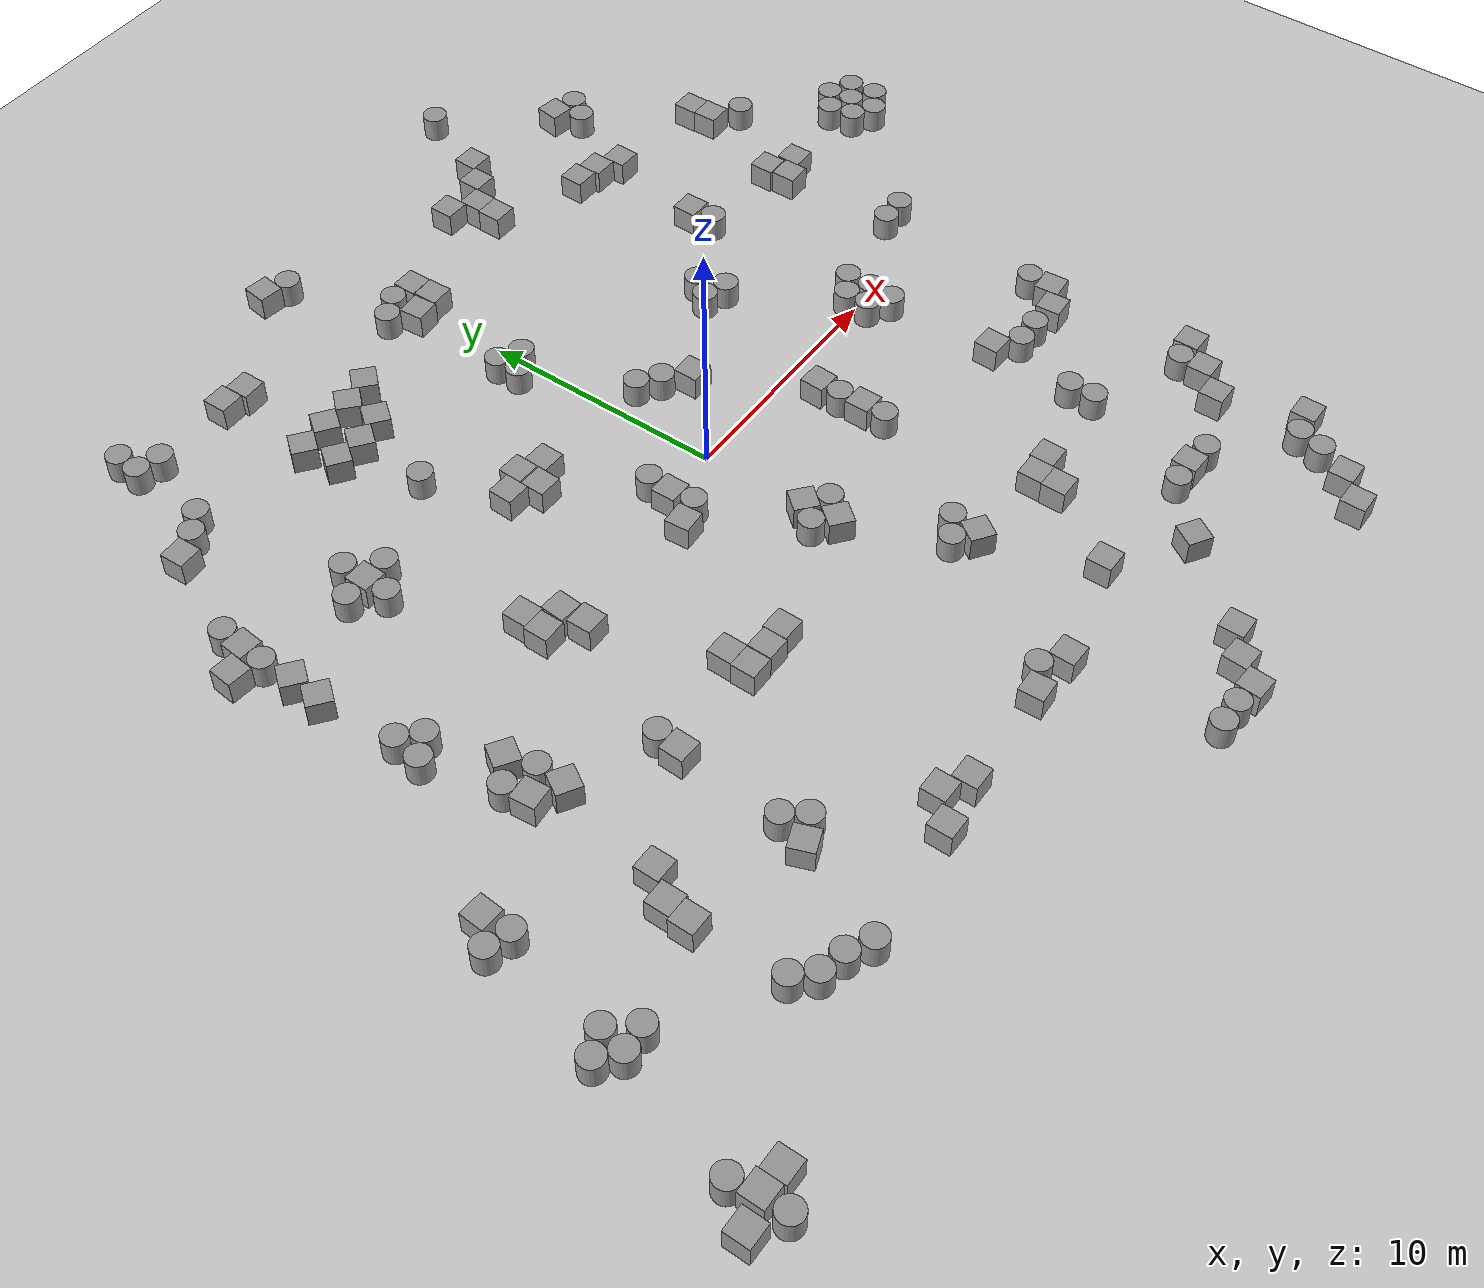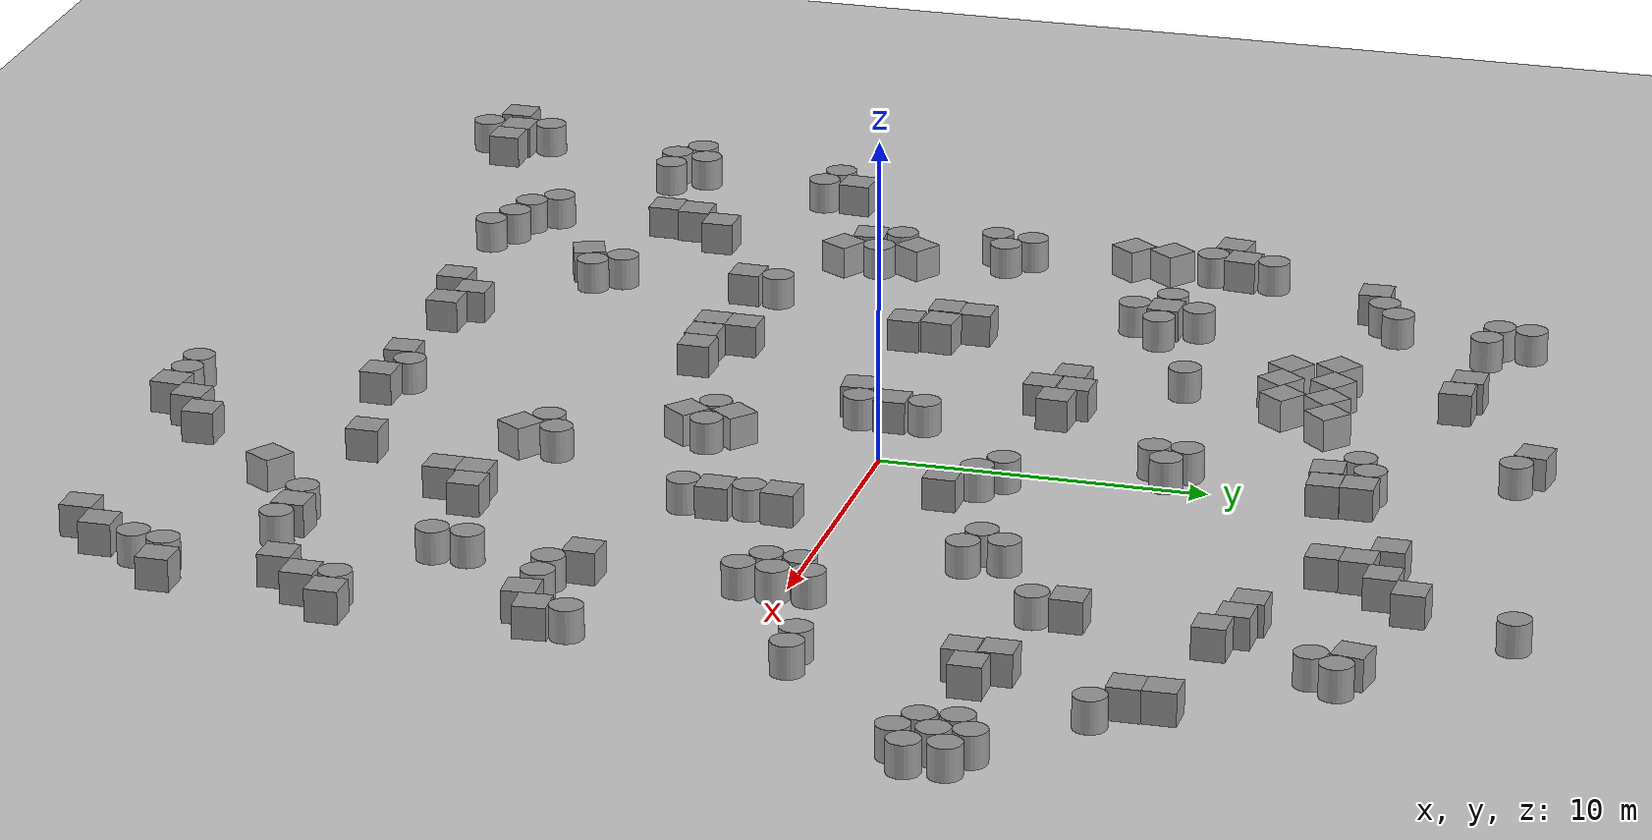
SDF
<sdf version="1.6">
 <world name="default">
  <light name="sun" type="directional">
   <pose>0 0 10 0 -0 0</pose>
   <diffuse>0.8 0.8 0.8 1</diffuse>
   <specular>0.1 0.1 0.1 1</specular>
   <attenuation>
    <range>1000</range>
    <constant>0.9</constant>
    <linear>0.01</linear>
    <quadratic>0.001</quadratic>
   </attenuation>
   <direction>-0.5 0.5 -1</direction>
  </light>
  <model name="ground_plane">
   <static>1</static>
   <link name="link">
    <collision name="collision">
     <geometry><plane><normal>0 0 1</normal><size>100 100</size></plane></geometry>
     <surface><friction><ode><mu>100</mu><mu2>50</mu2></ode></friction></surface>
    </collision>
    <visual name="visual">
     <cast_shadows>0</cast_shadows>
     <geometry><plane><normal>0 0 1</normal><size>100 100</size></plane></geometry>
     <material>
      <script><uri>file://media/materials/scripts/gazebo.material</uri><name>Gazebo/Grey</name></script>
     </material>
    </visual>
   </link>
  </model>
  <gravity>0 0 -9.8</gravity>
  <magnetic_field>6e-06 2.3e-05 -4.2e-05</magnetic_field>
  <atmosphere type="adiabatic"/>
  <physics name="default_physics" default="0" type="ode">
   <max_step_size>0.003</max_step_size>
   <real_time_factor>2</real_time_factor>
   <real_time_update_rate>1000</real_time_update_rate>
  </physics>
  <scene><ambient>0.4 0.4 0.4 1</ambient><background>0.7 0.7 0.7 1</background><shadows>1</shadows></scene>
  <spherical_coordinates>
   <surface_model>EARTH_WGS84</surface_model>
   <latitude_deg>0</latitude_deg>
   <longitude_deg>0</longitude_deg>
   <elevation>0</elevation>
   <heading_deg>0</heading_deg>
  </spherical_coordinates>
  <model name="unit_box_1">
   <pose>-5.11694 4.7861 0.5 0 0 -0.03385</pose>
   <link name="link">
    <inertial>
     <mass>1</mass>
     <inertia>
      <ixx>0.166667</ixx>
      <ixy>0</ixy>
      <ixz>0</ixz>
      <iyy>0.166667</iyy>
      <iyz>0</iyz>
      <izz>0.166667</izz>
     </inertia>
    </inertial>
    <collision name="collision"><geometry><box><size>1 1 1</size></box></geometry></collision>
    <visual name="visual">
     <geometry><box><size>1 1 1</size></box></geometry>
     <material>
      <script><name>Gazebo/Grey</name><uri>file://media/materials/scripts/gazebo.material</uri></script>
     </material>
    </visual>
   </link>
  </model>
  <model name="unit_box_2">
   <pose>-5.15243 3.73753 0.5 0 0 -0.033765</pose>
   <link name="link">
    <inertial>
     <mass>1</mass>
     <inertia>
      <ixx>0.166667</ixx>
      <ixy>0</ixy>
      <ixz>0</ixz>
      <iyy>0.166667</iyy>
      <iyz>0</iyz>
      <izz>0.166667</izz>
     </inertia>
    </inertial>
    <collision name="collision"><geometry><box><size>1 1 1</size></box></geometry></collision>
    <visual name="visual">
     <geometry><box><size>1 1 1</size></box></geometry>
     <material>
      <script><name>Gazebo/Grey</name><uri>file://media/materials/scripts/gazebo.material</uri></script>
     </material>
    </visual>
   </link>
  </model>
  <model name="unit_box_5">
   <pose>-6.52677 -7.31553 0.5 0 0 -0.01529</pose>
   <link name="link">
    <inertial>
     <mass>1</mass>
     <inertia>
      <ixx>0.166667</ixx>
      <ixy>0</ixy>
      <ixz>0</ixz>
      <iyy>0.166667</iyy>
      <iyz>0</iyz>
      <izz>0.166667</izz>
     </inertia>
    </inertial>
    <collision name="collision"><geometry><box><size>1 1 1</size></box></geometry></collision>
    <visual name="visual">
     <geometry><box><size>1 1 1</size></box></geometry>
     <material>
      <script><name>Gazebo/Grey</name><uri>file://media/materials/scripts/gazebo.material</uri></script>
     </material>
    </visual>
   </link>
  </model>
  <model name="unit_cylinder_0">
   <pose>10.7483 -0.233952 0.499942 0 -0 0.018874</pose>
   <link name="link">
    <inertial>
     <mass>1</mass>
     <inertia><ixx>0.145833</ixx><ixy>0</ixy><ixz>0</ixz><iyy>0.145833</iyy><iyz>0</iyz><izz>0.125</izz></inertia>
    </inertial>
    <collision name="collision">
     <geometry><cylinder><radius>0.5</radius><length>1</length></cylinder></geometry>
    </collision>
    <visual name="visual">
     <geometry><cylinder><radius>0.5</radius><length>1</length></cylinder></geometry>
     <material>
      <script><name>Gazebo/Grey</name><uri>file://media/materials/scripts/gazebo.material</uri></script>
     </material>
    </visual>
   </link>
  </model>
  <model name="unit_cylinder_1">
   <pose>10.5673 -10.4506 0.499942 0 0 -0.000248</pose>
   <link name="link">
    <inertial>
     <mass>1</mass>
     <inertia><ixx>0.145833</ixx><ixy>0</ixy><ixz>0</ixz><iyy>0.145833</iyy><iyz>0</iyz><izz>0.125</izz></inertia>
    </inertial>
    <collision name="collision">
     <geometry><cylinder><radius>0.5</radius><length>1</length></cylinder></geometry>
    </collision>
    <visual name="visual">
     <geometry><cylinder><radius>0.5</radius><length>1</length></cylinder></geometry>
     <material>
      <script><name>Gazebo/Grey</name><uri>file://media/materials/scripts/gazebo.material</uri></script>
     </material>
    </visual>
   </link>
  </model>
  <model name="unit_cylinder_2">
   <pose>10.5614 -9.39908 0.499942 0 0 -0.000915</pose>
   <link name="link">
    <inertial>
     <mass>1</mass>
     <inertia><ixx>0.145833</ixx><ixy>0</ixy><ixz>0</ixz><iyy>0.145833</iyy><iyz>0</iyz><izz>0.125</izz></inertia>
    </inertial>
    <collision name="collision">
     <geometry><cylinder><radius>0.5</radius><length>1</length></cylinder></geometry>
    </collision>
    <visual name="visual">
     <geometry><cylinder><radius>0.5</radius><length>1</length></cylinder></geometry>
     <material>
      <script><name>Gazebo/Grey</name><uri>file://media/materials/scripts/gazebo.material</uri></script>
     </material>
    </visual>
   </link>
  </model>
  <model name="unit_cylinder_3">
   <pose>10.6757 -1.26585 0.499942 0 -0 0.000199</pose>
   <link name="link">
    <inertial>
     <mass>1</mass>
     <inertia><ixx>0.145833</ixx><ixy>0</ixy><ixz>0</ixz><iyy>0.145833</iyy><iyz>0</iyz><izz>0.125</izz></inertia>
    </inertial>
    <collision name="collision">
     <geometry><cylinder><radius>0.5</radius><length>1</length></cylinder></geometry>
    </collision>
    <visual name="visual">
     <geometry><cylinder><radius>0.5</radius><length>1</length></cylinder></geometry>
     <material>
      <script><name>Gazebo/Grey</name><uri>file://media/materials/scripts/gazebo.material</uri></script>
     </material>
    </visual>
   </link>
  </model>
  <model name="unit_cylinder_4">
   <pose>10.7497 0.834589 0.499942 0 0 -0.022066</pose>
   <link name="link">
    <inertial>
     <mass>1</mass>
     <inertia><ixx>0.145833</ixx><ixy>0</ixy><ixz>0</ixz><iyy>0.145833</iyy><iyz>0</iyz><izz>0.125</izz></inertia>
    </inertial>
    <collision name="collision">
     <geometry><cylinder><radius>0.5</radius><length>1</length></cylinder></geometry>
    </collision>
    <visual name="visual">
     <geometry><cylinder><radius>0.5</radius><length>1</length></cylinder></geometry>
     <material>
      <script><name>Gazebo/Grey</name><uri>file://media/materials/scripts/gazebo.material</uri></script>
     </material>
    </visual>
   </link>
  </model>
  <model name="unit_box_8">
   <pose>-9.3394 -0.54228 0.5 0 0 -0.074039</pose>
   <link name="link">
    <inertial>
     <mass>1</mass>
     <inertia>
      <ixx>0.166667</ixx>
      <ixy>0</ixy>
      <ixz>0</ixz>
      <iyy>0.166667</iyy>
      <iyz>0</iyz>
      <izz>0.166667</izz>
     </inertia>
    </inertial>
    <collision name="collision"><geometry><box><size>1 1 1</size></box></geometry></collision>
    <visual name="visual">
     <geometry><box><size>1 1 1</size></box></geometry>
     <material>
      <script><name>Gazebo/Grey</name><uri>file://media/materials/scripts/gazebo.material</uri></script>
     </material>
    </visual>
   </link>
  </model>
  <model name="unit_cylinder_6">
   <pose>-2.57686 0.723564 0.499942 0 0 -0.000453</pose>
   <link name="link">
    <inertial>
     <mass>1</mass>
     <inertia><ixx>0.145833</ixx><ixy>0</ixy><ixz>0</ixz><iyy>0.145833</iyy><iyz>0</iyz><izz>0.125</izz></inertia>
    </inertial>
    <collision name="collision">
     <geometry><cylinder><radius>0.5</radius><length>1</length></cylinder></geometry>
    </collision>
    <visual name="visual">
     <geometry><cylinder><radius>0.5</radius><length>1</length></cylinder></geometry>
     <material>
      <script><name>Gazebo/Grey</name><uri>file://media/materials/scripts/gazebo.material</uri></script>
     </material>
    </visual>
   </link>
  </model>
  <model name="unit_box_9">
   <pose>2.80573 2.69051 0.5 0 0 -0.00823</pose>
   <link name="link">
    <inertial>
     <mass>1</mass>
     <inertia>
      <ixx>0.166667</ixx>
      <ixy>0</ixy>
      <ixz>0</ixz>
      <iyy>0.166667</iyy>
      <iyz>0</iyz>
      <izz>0.166667</izz>
     </inertia>
    </inertial>
    <collision name="collision"><geometry><box><size>1 1 1</size></box></geometry></collision>
    <visual name="visual">
     <geometry><box><size>1 1 1</size></box></geometry>
     <material>
      <script><name>Gazebo/Grey</name><uri>file://media/materials/scripts/gazebo.material</uri></script>
     </material>
    </visual>
   </link>
  </model>
  <model name="unit_cylinder_7">
   <pose>1.38178 -9.82712 0.499942 0 0 -0.019752</pose>
   <link name="link">
    <inertial>
     <mass>1</mass>
     <inertia><ixx>0.145833</ixx><ixy>0</ixy><ixz>0</ixz><iyy>0.145833</iyy><iyz>0</iyz><izz>0.125</izz></inertia>
    </inertial>
    <collision name="collision">
     <geometry><cylinder><radius>0.5</radius><length>1</length></cylinder></geometry>
    </collision>
    <visual name="visual">
     <geometry><cylinder><radius>0.5</radius><length>1</length></cylinder></geometry>
     <material>
      <script><name>Gazebo/Grey</name><uri>file://media/materials/scripts/gazebo.material</uri></script>
     </material>
    </visual>
   </link>
  </model>
  <model name="unit_box_10">
   <pose>6.83774 -10.6024 0.5 0 0 -2.4e-05</pose>
   <link name="link">
    <inertial>
     <mass>1</mass>
     <inertia>
      <ixx>0.166667</ixx>
      <ixy>0</ixy>
      <ixz>0</ixz>
      <iyy>0.166667</iyy>
      <iyz>0</iyz>
      <izz>0.166667</izz>
     </inertia>
    </inertial>
    <collision name="collision"><geometry><box><size>1 1 1</size></box></geometry></collision>
    <visual name="visual">
     <geometry><box><size>1 1 1</size></box></geometry>
     <material>
      <script><name>Gazebo/Grey</name><uri>file://media/materials/scripts/gazebo.material</uri></script>
     </material>
    </visual>
   </link>
  </model>
  <model name="unit_box_11">
   <pose>5.82225 -11.6823 0.5 0 0 -3.2e-05</pose>
   <link name="link">
    <inertial>
     <mass>1</mass>
     <inertia>
      <ixx>0.166667</ixx>
      <ixy>0</ixy>
      <ixz>0</ixz>
      <iyy>0.166667</iyy>
      <iyz>0</iyz>
      <izz>0.166667</izz>
     </inertia>
    </inertial>
    <collision name="collision"><geometry><box><size>1 1 1</size></box></geometry></collision>
    <visual name="visual">
     <geometry><box><size>1 1 1</size></box></geometry>
     <material>
      <script><name>Gazebo/Grey</name><uri>file://media/materials/scripts/gazebo.material</uri></script>
     </material>
    </visual>
   </link>
  </model>
  <model name="unit_cylinder_8_0">
   <pose>-0.145957 8.69713 0.499942 0 0 -0.118352</pose>
   <link name="link">
    <inertial>
     <mass>1</mass>
     <inertia><ixx>0.145833</ixx><ixy>0</ixy><ixz>0</ixz><iyy>0.145833</iyy><iyz>0</iyz><izz>0.125</izz></inertia>
    </inertial>
    <collision name="collision">
     <geometry><cylinder><radius>0.5</radius><length>1</length></cylinder></geometry>
    </collision>
    <visual name="visual">
     <geometry><cylinder><radius>0.5</radius><length>1</length></cylinder></geometry>
     <material>
      <script><name>Gazebo/Grey</name><uri>file://media/materials/scripts/gazebo.material</uri></script>
     </material>
    </visual>
   </link>
  </model>
  <model name="unit_box_12">
   <pose>5.15723 -1.54455 0.5 0 0 -0.056775</pose>
   <link name="link">
    <inertial>
     <mass>1</mass>
     <inertia>
      <ixx>0.166667</ixx>
      <ixy>0</ixy>
      <ixz>0</ixz>
      <iyy>0.166667</iyy>
      <iyz>0</iyz>
      <izz>0.166667</izz>
     </inertia>
    </inertial>
    <collision name="collision"><geometry><box><size>1 1 1</size></box></geometry></collision>
    <visual name="visual">
     <geometry><box><size>1 1 1</size></box></geometry>
     <material>
      <script><name>Gazebo/Grey</name><uri>file://media/materials/scripts/gazebo.material</uri></script>
     </material>
    </visual>
   </link>
  </model>
  <model name="unit_cylinder_8_1">
   <pose>5.09818 -2.54286 0.499942 0 0 -0.000545</pose>
   <link name="link">
    <inertial>
     <mass>1</mass>
     <inertia><ixx>0.145833</ixx><ixy>0</ixy><ixz>0</ixz><iyy>0.145833</iyy><iyz>0</iyz><izz>0.125</izz></inertia>
    </inertial>
    <collision name="collision">
     <geometry><cylinder><radius>0.5</radius><length>1</length></cylinder></geometry>
    </collision>
    <visual name="visual">
     <geometry><cylinder><radius>0.5</radius><length>1</length></cylinder></geometry>
     <material>
      <script><name>Gazebo/Grey</name><uri>file://media/materials/scripts/gazebo.material</uri></script>
     </material>
    </visual>
   </link>
  </model>
  <model name="unit_box_13">
   <pose>5.186 -3.54449 0.5 0 0 -0.016738</pose>
   <link name="link">
    <inertial>
     <mass>1</mass>
     <inertia>
      <ixx>0.166667</ixx>
      <ixy>0</ixy>
      <ixz>0</ixz>
      <iyy>0.166667</iyy>
      <iyz>0</iyz>
      <izz>0.166667</izz>
     </inertia>
    </inertial>
    <collision name="collision"><geometry><box><size>1 1 1</size></box></geometry></collision>
    <visual name="visual">
     <geometry><box><size>1 1 1</size></box></geometry>
     <material>
      <script><name>Gazebo/Grey</name><uri>file://media/materials/scripts/gazebo.material</uri></script>
     </material>
    </visual>
   </link>
  </model>
  <model name="unit_cylinder_8_2">
   <pose>5.13166 -4.54376 0.499942 0 0 -0.00034</pose>
   <link name="link">
    <inertial>
     <mass>1</mass>
     <inertia><ixx>0.145833</ixx><ixy>0</ixy><ixz>0</ixz><iyy>0.145833</iyy><iyz>0</iyz><izz>0.125</izz></inertia>
    </inertial>
    <collision name="collision">
     <geometry><cylinder><radius>0.5</radius><length>1</length></cylinder></geometry>
    </collision>
    <visual name="visual">
     <geometry><cylinder><radius>0.5</radius><length>1</length></cylinder></geometry>
     <material>
      <script><name>Gazebo/Grey</name><uri>file://media/materials/scripts/gazebo.material</uri></script>
     </material>
    </visual>
   </link>
  </model>
  <model name="unit_box_14">
   <pose>5.83773 -10.6822 0.5 0 0 -2.8e-05</pose>
   <link name="link">
    <inertial>
     <mass>1</mass>
     <inertia>
      <ixx>0.166667</ixx>
      <ixy>0</ixy>
      <ixz>0</ixz>
      <iyy>0.166667</iyy>
      <iyz>0</iyz>
      <izz>0.166667</izz>
     </inertia>
    </inertial>
    <collision name="collision"><geometry><box><size>1 1 1</size></box></geometry></collision>
    <visual name="visual">
     <geometry><box><size>1 1 1</size></box></geometry>
     <material>
      <script><name>Gazebo/Grey</name><uri>file://media/materials/scripts/gazebo.material</uri></script>
     </material>
    </visual>
   </link>
  </model>
  <model name="unit_box_15">
   <pose>-10.3952 -0.600275 0.5 0 0 -0.001077</pose>
   <link name="link">
    <inertial>
     <mass>1</mass>
     <inertia>
      <ixx>0.166667</ixx>
      <ixy>0</ixy>
      <ixz>0</ixz>
      <iyy>0.166667</iyy>
      <iyz>0</iyz>
      <izz>0.166667</izz>
     </inertia>
    </inertial>
    <collision name="collision"><geometry><box><size>1 1 1</size></box></geometry></collision>
    <visual name="visual">
     <geometry><box><size>1 1 1</size></box></geometry>
     <material>
      <script><name>Gazebo/Grey</name><uri>file://media/materials/scripts/gazebo.material</uri></script>
     </material>
    </visual>
   </link>
  </model>
  <model name="unit_box_19">
   <pose>-18.0601 6.84386 0.5 0 0 -0.095919</pose>
   <link name="link">
    <inertial>
     <mass>1</mass>
     <inertia>
      <ixx>0.166667</ixx>
      <ixy>0</ixy>
      <ixz>0</ixz>
      <iyy>0.166667</iyy>
      <iyz>0</iyz>
      <izz>0.166667</izz>
     </inertia>
    </inertial>
    <collision name="collision"><geometry><box><size>1 1 1</size></box></geometry></collision>
    <visual name="visual">
     <geometry><box><size>1 1 1</size></box></geometry>
     <material>
      <script><name>Gazebo/Grey</name><uri>file://media/materials/scripts/gazebo.material</uri></script>
     </material>
    </visual>
   </link>
  </model>
  <model name="unit_box_23">
   <pose>9.27836 13.3022 0.5 0 0 -0.004743</pose>
   <link name="link">
    <inertial>
     <mass>1</mass>
     <inertia>
      <ixx>0.166667</ixx>
      <ixy>0</ixy>
      <ixz>0</ixz>
      <iyy>0.166667</iyy>
      <iyz>0</iyz>
      <izz>0.166667</izz>
     </inertia>
    </inertial>
    <collision name="collision"><geometry><box><size>1 1 1</size></box></geometry></collision>
    <visual name="visual">
     <geometry><box><size>1 1 1</size></box></geometry>
     <material>
      <script><name>Gazebo/Grey</name><uri>file://media/materials/scripts/gazebo.material</uri></script>
     </material>
    </visual>
   </link>
  </model>
  <model name="unit_cylinder_13">
   <pose>14.6463 1.55239 0.499942 0 -0 0.00046</pose>
   <link name="link">
    <inertial>
     <mass>1</mass>
     <inertia><ixx>0.145833</ixx><ixy>0</ixy><ixz>0</ixz><iyy>0.145833</iyy><iyz>0</iyz><izz>0.125</izz></inertia>
    </inertial>
    <collision name="collision">
     <geometry><cylinder><radius>0.5</radius><length>1</length></cylinder></geometry>
    </collision>
    <visual name="visual">
     <geometry><cylinder><radius>0.5</radius><length>1</length></cylinder></geometry>
     <material>
      <script><name>Gazebo/Grey</name><uri>file://media/materials/scripts/gazebo.material</uri></script>
     </material>
    </visual>
   </link>
  </model>
  <model name="unit_cylinder_14">
   <pose>14.9355 -5.05121 0.499942 0 -0 0.002226</pose>
   <link name="link">
    <inertial>
     <mass>1</mass>
     <inertia><ixx>0.145833</ixx><ixy>0</ixy><ixz>0</ixz><iyy>0.145833</iyy><iyz>0</iyz><izz>0.125</izz></inertia>
    </inertial>
    <collision name="collision">
     <geometry><cylinder><radius>0.5</radius><length>1</length></cylinder></geometry>
    </collision>
    <visual name="visual">
     <geometry><cylinder><radius>0.5</radius><length>1</length></cylinder></geometry>
     <material>
      <script><name>Gazebo/Grey</name><uri>file://media/materials/scripts/gazebo.material</uri></script>
     </material>
    </visual>
   </link>
  </model>
  <model name="unit_box_25">
   <pose>13.9445 -6.67344 0.5 0 -0 0.075178</pose>
   <link name="link">
    <inertial>
     <mass>1</mass>
     <inertia>
      <ixx>0.166667</ixx>
      <ixy>0</ixy>
      <ixz>0</ixz>
      <iyy>0.166667</iyy>
      <iyz>0</iyz>
      <izz>0.166667</izz>
     </inertia>
    </inertial>
    <collision name="collision"><geometry><box><size>1 1 1</size></box></geometry></collision>
    <visual name="visual">
     <geometry><box><size>1 1 1</size></box></geometry>
     <material>
      <script><name>Gazebo/Grey</name><uri>file://media/materials/scripts/gazebo.material</uri></script>
     </material>
    </visual>
   </link>
  </model>
  <model name="unit_box_26">
   <pose>3.65039 -14.8069 0.5 0 -0 0</pose>
   <link name="link">
    <inertial>
     <mass>1</mass>
     <inertia>
      <ixx>0.166667</ixx>
      <ixy>0</ixy>
      <ixz>0</ixz>
      <iyy>0.166667</iyy>
      <iyz>0</iyz>
      <izz>0.166667</izz>
     </inertia>
    </inertial>
    <collision name="collision"><geometry><box><size>1 1 1</size></box></geometry></collision>
    <visual name="visual">
     <geometry><box><size>1 1 1</size></box></geometry>
     <material>
      <script><name>Gazebo/Grey</name><uri>file://media/materials/scripts/gazebo.material</uri></script>
     </material>
    </visual>
   </link>
  </model>
  <model name="unit_cylinder_15">
   <pose>-1.77956 -15.2792 0.499942 0 0 -0.00561</pose>
   <link name="link">
    <inertial>
     <mass>1</mass>
     <inertia><ixx>0.145833</ixx><ixy>0</ixy><ixz>0</ixz><iyy>0.145833</iyy><iyz>0</iyz><izz>0.125</izz></inertia>
    </inertial>
    <collision name="collision">
     <geometry><cylinder><radius>0.5</radius><length>1</length></cylinder></geometry>
    </collision>
    <visual name="visual">
     <geometry><cylinder><radius>0.5</radius><length>1</length></cylinder></geometry>
     <material>
      <script><name>Gazebo/Grey</name><uri>file://media/materials/scripts/gazebo.material</uri></script>
     </material>
    </visual>
   </link>
  </model>
  <model name="unit_box_27">
   <pose>-7.07555 -15.8653 0.5 0 -0 0</pose>
   <link name="link">
    <inertial>
     <mass>1</mass>
     <inertia>
      <ixx>0.166667</ixx>
      <ixy>0</ixy>
      <ixz>0</ixz>
      <iyy>0.166667</iyy>
      <iyz>0</iyz>
      <izz>0.166667</izz>
     </inertia>
    </inertial>
    <collision name="collision"><geometry><box><size>1 1 1</size></box></geometry></collision>
    <visual name="visual">
     <geometry><box><size>1 1 1</size></box></geometry>
     <material>
      <script><name>Gazebo/Grey</name><uri>file://media/materials/scripts/gazebo.material</uri></script>
     </material>
    </visual>
   </link>
  </model>
  <model name="unit_cylinder_16">
   <pose>-11.4365 -12.4394 0.499942 0 0 -0.038077</pose>
   <link name="link">
    <inertial>
     <mass>1</mass>
     <inertia><ixx>0.145833</ixx><ixy>0</ixy><ixz>0</ixz><iyy>0.145833</iyy><iyz>0</iyz><izz>0.125</izz></inertia>
    </inertial>
    <collision name="collision">
     <geometry><cylinder><radius>0.5</radius><length>1</length></cylinder></geometry>
    </collision>
    <visual name="visual">
     <geometry><cylinder><radius>0.5</radius><length>1</length></cylinder></geometry>
     <material>
      <script><name>Gazebo/Grey</name><uri>file://media/materials/scripts/gazebo.material</uri></script>
     </material>
    </visual>
   </link>
  </model>
  <model name="unit_cylinder_17">
   <pose>-16.3151 -3.60972 0.499942 0 0 -0.047387</pose>
   <link name="link">
    <inertial>
     <mass>1</mass>
     <inertia><ixx>0.145833</ixx><ixy>0</ixy><ixz>0</ixz><iyy>0.145833</iyy><iyz>0</iyz><izz>0.125</izz></inertia>
    </inertial>
    <collision name="collision">
     <geometry><cylinder><radius>0.5</radius><length>1</length></cylinder></geometry>
    </collision>
    <visual name="visual">
     <geometry><cylinder><radius>0.5</radius><length>1</length></cylinder></geometry>
     <material>
      <script><name>Gazebo/Grey</name><uri>file://media/materials/scripts/gazebo.material</uri></script>
     </material>
    </visual>
   </link>
  </model>
  <model name="unit_cylinder_18">
   <pose>-17.0713 -0.679046 0.499942 0 0 -0.070732</pose>
   <link name="link">
    <inertial>
     <mass>1</mass>
     <inertia><ixx>0.145833</ixx><ixy>0</ixy><ixz>0</ixz><iyy>0.145833</iyy><iyz>0</iyz><izz>0.125</izz></inertia>
    </inertial>
    <collision name="collision">
     <geometry><cylinder><radius>0.5</radius><length>1</length></cylinder></geometry>
    </collision>
    <visual name="visual">
     <geometry><cylinder><radius>0.5</radius><length>1</length></cylinder></geometry>
     <material>
      <script><name>Gazebo/Grey</name><uri>file://media/materials/scripts/gazebo.material</uri></script>
     </material>
    </visual>
   </link>
  </model>
  <model name="unit_cylinder_19">
   <pose>15.6462 1.57109 0.499942 0 0 -0.001342</pose>
   <link name="link">
    <inertial>
     <mass>1</mass>
     <inertia><ixx>0.145833</ixx><ixy>0</ixy><ixz>0</ixz><iyy>0.145833</iyy><iyz>0</iyz><izz>0.125</izz></inertia>
    </inertial>
    <collision name="collision">
     <geometry><cylinder><radius>0.5</radius><length>1</length></cylinder></geometry>
    </collision>
    <visual name="visual">
     <geometry><cylinder><radius>0.5</radius><length>1</length></cylinder></geometry>
     <material>
      <script><name>Gazebo/Grey</name><uri>file://media/materials/scripts/gazebo.material</uri></script>
     </material>
    </visual>
   </link>
  </model>
  <model name="unit_box_30">
   <pose>15.8822 11.2878 0.5 0 -0 0.004435</pose>
   <link name="link">
    <inertial>
     <mass>1</mass>
     <inertia>
      <ixx>0.166667</ixx>
      <ixy>0</ixy>
      <ixz>0</ixz>
      <iyy>0.166667</iyy>
      <iyz>0</iyz>
      <izz>0.166667</izz>
     </inertia>
    </inertial>
    <collision name="collision"><geometry><box><size>1 1 1</size></box></geometry></collision>
    <visual name="visual">
     <geometry><box><size>1 1 1</size></box></geometry>
     <material>
      <script><name>Gazebo/Grey</name><uri>file://media/materials/scripts/gazebo.material</uri></script>
     </material>
    </visual>
   </link>
  </model>
  <model name="unit_cylinder_20">
   <pose>16.9697 10.5115 0.499942 0 -0 0</pose>
   <link name="link">
    <inertial>
     <mass>1</mass>
     <inertia><ixx>0.145833</ixx><ixy>0</ixy><ixz>0</ixz><iyy>0.145833</iyy><iyz>0</iyz><izz>0.125</izz></inertia>
    </inertial>
    <collision name="collision">
     <geometry><cylinder><radius>0.5</radius><length>1</length></cylinder></geometry>
    </collision>
    <visual name="visual">
     <geometry><cylinder><radius>0.5</radius><length>1</length></cylinder></geometry>
     <material>
      <script><name>Gazebo/Grey</name><uri>file://media/materials/scripts/gazebo.material</uri></script>
     </material>
    </visual>
   </link>
  </model>
  <model name="unit_box_32">
   <pose>10.2775 13.1122 0.5 0 0 -0.004735</pose>
   <link name="link">
    <inertial>
     <mass>1</mass>
     <inertia>
      <ixx>0.166667</ixx>
      <ixy>0</ixy>
      <ixz>0</ixz>
      <iyy>0.166667</iyy>
      <iyz>0</iyz>
      <izz>0.166667</izz>
     </inertia>
    </inertial>
    <collision name="collision"><geometry><box><size>1 1 1</size></box></geometry></collision>
    <visual name="visual">
     <geometry><box><size>1 1 1</size></box></geometry>
     <material>
      <script><name>Gazebo/Grey</name><uri>file://media/materials/scripts/gazebo.material</uri></script>
     </material>
    </visual>
   </link>
  </model>
  <model name="unit_cylinder_23">
   <pose>-15.0481 -4.04748 0.499942 0 -0 0.013755</pose>
   <link name="link">
    <inertial>
     <mass>1</mass>
     <inertia><ixx>0.145833</ixx><ixy>0</ixy><ixz>0</ixz><iyy>0.145833</iyy><iyz>0</iyz><izz>0.125</izz></inertia>
    </inertial>
    <collision name="collision">
     <geometry><cylinder><radius>0.5</radius><length>1</length></cylinder></geometry>
    </collision>
    <visual name="visual">
     <geometry><cylinder><radius>0.5</radius><length>1</length></cylinder></geometry>
     <material>
      <script><name>Gazebo/Grey</name><uri>file://media/materials/scripts/gazebo.material</uri></script>
     </material>
    </visual>
   </link>
  </model>
  <model name="unit_cylinder_24">
   <pose>-16.9163 0.507461 0.499942 0 -0 0.1365</pose>
   <link name="link">
    <inertial>
     <mass>1</mass>
     <inertia><ixx>0.145833</ixx><ixy>0</ixy><ixz>0</ixz><iyy>0.145833</iyy><iyz>0</iyz><izz>0.125</izz></inertia>
    </inertial>
    <collision name="collision">
     <geometry><cylinder><radius>0.5</radius><length>1</length></cylinder></geometry>
    </collision>
    <visual name="visual">
     <geometry><cylinder><radius>0.5</radius><length>1</length></cylinder></geometry>
     <material>
      <script><name>Gazebo/Grey</name><uri>file://media/materials/scripts/gazebo.material</uri></script>
     </material>
    </visual>
   </link>
  </model>
  <model name="unit_box_35">
   <pose>14.9026 -6.05619 0.5 0 -0 0.071763</pose>
   <link name="link">
    <inertial>
     <mass>1</mass>
     <inertia>
      <ixx>0.166667</ixx>
      <ixy>0</ixy>
      <ixz>0</ixz>
      <iyy>0.166667</iyy>
      <iyz>0</iyz>
      <izz>0.166667</izz>
     </inertia>
    </inertial>
    <collision name="collision"><geometry><box><size>1 1 1</size></box></geometry></collision>
    <visual name="visual">
     <geometry><box><size>1 1 1</size></box></geometry>
     <material>
      <script><name>Gazebo/Grey</name><uri>file://media/materials/scripts/gazebo.material</uri></script>
     </material>
    </visual>
   </link>
  </model>
  <model name="unit_box_24_0">
   <pose>14.4861 7.34424 0.5 0 -0 0</pose>
   <link name="link">
    <inertial>
     <mass>1</mass>
     <inertia>
      <ixx>0.166667</ixx>
      <ixy>0</ixy>
      <ixz>0</ixz>
      <iyy>0.166667</iyy>
      <iyz>0</iyz>
      <izz>0.166667</izz>
     </inertia>
    </inertial>
    <collision name="collision"><geometry><box><size>1 1 1</size></box></geometry></collision>
    <visual name="visual">
     <geometry><box><size>1 1 1</size></box></geometry>
     <material>
      <script><name>Gazebo/Grey</name><uri>file://media/materials/scripts/gazebo.material</uri></script>
     </material>
    </visual>
   </link>
  </model>
  <model name="unit_box_24_1">
   <pose>14.5714 6.30894 0.5 0 -0 0.003235</pose>
   <link name="link">
    <inertial>
     <mass>1</mass>
     <inertia>
      <ixx>0.166667</ixx>
      <ixy>0</ixy>
      <ixz>0</ixz>
      <iyy>0.166667</iyy>
      <iyz>0</iyz>
      <izz>0.166667</izz>
     </inertia>
    </inertial>
    <collision name="collision"><geometry><box><size>1 1 1</size></box></geometry></collision>
    <visual name="visual">
     <geometry><box><size>1 1 1</size></box></geometry>
     <material>
      <script><name>Gazebo/Grey</name><uri>file://media/materials/scripts/gazebo.material</uri></script>
     </material>
    </visual>
   </link>
  </model>
  <model name="unit_box_24_2">
   <pose>-8.1048 -15.29 0.5 0 0 -6e-06</pose>
   <link name="link">
    <inertial>
     <mass>1</mass>
     <inertia>
      <ixx>0.166667</ixx>
      <ixy>0</ixy>
      <ixz>0</ixz>
      <iyy>0.166667</iyy>
      <iyz>0</iyz>
      <izz>0.166667</izz>
     </inertia>
    </inertial>
    <collision name="collision"><geometry><box><size>1 1 1</size></box></geometry></collision>
    <visual name="visual">
     <geometry><box><size>1 1 1</size></box></geometry>
     <material>
      <script><name>Gazebo/Grey</name><uri>file://media/materials/scripts/gazebo.material</uri></script>
     </material>
    </visual>
   </link>
  </model>
  <model name="unit_box_24">
   <pose>-12.3767 -12.8516 0.5 0 -0 0.358388</pose>
   <link name="link">
    <inertial>
     <mass>1</mass>
     <inertia>
      <ixx>0.166667</ixx>
      <ixy>0</ixy>
      <ixz>0</ixz>
      <iyy>0.166667</iyy>
      <iyz>0</iyz>
      <izz>0.166667</izz>
     </inertia>
    </inertial>
    <collision name="collision"><geometry><box><size>1 1 1</size></box></geometry></collision>
    <visual name="visual">
     <geometry><box><size>1 1 1</size></box></geometry>
     <material>
      <script><name>Gazebo/Grey</name><uri>file://media/materials/scripts/gazebo.material</uri></script>
     </material>
    </visual>
   </link>
  </model>
  <model name="unit_box_28_0">
   <pose>-16.7547 -10.5748 0.5 0 -0 0</pose>
   <link name="link">
    <inertial>
     <mass>1</mass>
     <inertia>
      <ixx>0.166667</ixx>
      <ixy>0</ixy>
      <ixz>0</ixz>
      <iyy>0.166667</iyy>
      <iyz>0</iyz>
      <izz>0.166667</izz>
     </inertia>
    </inertial>
    <collision name="collision"><geometry><box><size>1 1 1</size></box></geometry></collision>
    <visual name="visual">
     <geometry><box><size>1 1 1</size></box></geometry>
     <material>
      <script><name>Gazebo/Grey</name><uri>file://media/materials/scripts/gazebo.material</uri></script>
     </material>
    </visual>
   </link>
  </model>
  <model name="unit_box_28_1">
   <pose>-16.8633 -11.5756 0.5 0 -0 0</pose>
   <link name="link">
    <inertial>
     <mass>1</mass>
     <inertia>
      <ixx>0.166667</ixx>
      <ixy>0</ixy>
      <ixz>0</ixz>
      <iyy>0.166667</iyy>
      <iyz>0</iyz>
      <izz>0.166667</izz>
     </inertia>
    </inertial>
    <collision name="collision"><geometry><box><size>1 1 1</size></box></geometry></collision>
    <visual name="visual">
     <geometry><box><size>1 1 1</size></box></geometry>
     <material>
      <script><name>Gazebo/Grey</name><uri>file://media/materials/scripts/gazebo.material</uri></script>
     </material>
    </visual>
   </link>
  </model>
  <model name="unit_cylinder_27">
   <pose>-16.0304 -15.9217 0.499942 0 0 -4.4e-05</pose>
   <link name="link">
    <inertial>
     <mass>1</mass>
     <inertia><ixx>0.145833</ixx><ixy>0</ixy><ixz>0</ixz><iyy>0.145833</iyy><iyz>0</iyz><izz>0.125</izz></inertia>
    </inertial>
    <collision name="collision">
     <geometry><cylinder><radius>0.5</radius><length>1</length></cylinder></geometry>
    </collision>
    <visual name="visual">
     <geometry><cylinder><radius>0.5</radius><length>1</length></cylinder></geometry>
     <material>
      <script><name>Gazebo/Grey</name><uri>file://media/materials/scripts/gazebo.material</uri></script>
     </material>
    </visual>
   </link>
  </model>
  <model name="unit_cylinder_28">
   <pose>-15.0122 -16.1585 0.499942 0 -0 0</pose>
   <link name="link">
    <inertial>
     <mass>1</mass>
     <inertia><ixx>0.145833</ixx><ixy>0</ixy><ixz>0</ixz><iyy>0.145833</iyy><iyz>0</iyz><izz>0.125</izz></inertia>
    </inertial>
    <collision name="collision">
     <geometry><cylinder><radius>0.5</radius><length>1</length></cylinder></geometry>
    </collision>
    <visual name="visual">
     <geometry><cylinder><radius>0.5</radius><length>1</length></cylinder></geometry>
     <material>
      <script><name>Gazebo/Grey</name><uri>file://media/materials/scripts/gazebo.material</uri></script>
     </material>
    </visual>
   </link>
  </model>
  <model name="unit_cylinder_29">
   <pose>-14.0775 -16.6533 0.499942 0 -0 0</pose>
   <link name="link">
    <inertial>
     <mass>1</mass>
     <inertia><ixx>0.145833</ixx><ixy>0</ixy><ixz>0</ixz><iyy>0.145833</iyy><iyz>0</iyz><izz>0.125</izz></inertia>
    </inertial>
    <collision name="collision">
     <geometry><cylinder><radius>0.5</radius><length>1</length></cylinder></geometry>
    </collision>
    <visual name="visual">
     <geometry><cylinder><radius>0.5</radius><length>1</length></cylinder></geometry>
     <material>
      <script><name>Gazebo/Grey</name><uri>file://media/materials/scripts/gazebo.material</uri></script>
     </material>
    </visual>
   </link>
  </model>
  <model name="unit_cylinder_31">
   <pose>-12.0079 -11.6186 0.499942 0 0 -5.3e-05</pose>
   <link name="link">
    <inertial>
     <mass>1</mass>
     <inertia><ixx>0.145833</ixx><ixy>0</ixy><ixz>0</ixz><iyy>0.145833</iyy><iyz>0</iyz><izz>0.125</izz></inertia>
    </inertial>
    <collision name="collision">
     <geometry><cylinder><radius>0.5</radius><length>1</length></cylinder></geometry>
    </collision>
    <visual name="visual">
     <geometry><cylinder><radius>0.5</radius><length>1</length></cylinder></geometry>
     <material>
      <script><name>Gazebo/Grey</name><uri>file://media/materials/scripts/gazebo.material</uri></script>
     </material>
    </visual>
   </link>
  </model>
  <model name="unit_box_28">
   <pose>-15.9198 -9.53398 0.5 0 -0 0</pose>
   <link name="link">
    <inertial>
     <mass>1</mass>
     <inertia>
      <ixx>0.166667</ixx>
      <ixy>0</ixy>
      <ixz>0</ixz>
      <iyy>0.166667</iyy>
      <iyz>0</iyz>
      <izz>0.166667</izz>
     </inertia>
    </inertial>
    <collision name="collision"><geometry><box><size>1 1 1</size></box></geometry></collision>
    <visual name="visual">
     <geometry><box><size>1 1 1</size></box></geometry>
     <material>
      <script><name>Gazebo/Grey</name><uri>file://media/materials/scripts/gazebo.material</uri></script>
     </material>
    </visual>
   </link>
  </model>
  <model name="unit_box_34">
   <pose>-9.24528 -1.60585 0.5 0 -0 0</pose>
   <link name="link">
    <inertial>
     <mass>1</mass>
     <inertia>
      <ixx>0.166667</ixx>
      <ixy>0</ixy>
      <ixz>0</ixz>
      <iyy>0.166667</iyy>
      <iyz>0</iyz>
      <izz>0.166667</izz>
     </inertia>
    </inertial>
    <collision name="collision"><geometry><box><size>1 1 1</size></box></geometry></collision>
    <visual name="visual">
     <geometry><box><size>1 1 1</size></box></geometry>
     <material>
      <script><name>Gazebo/Grey</name><uri>file://media/materials/scripts/gazebo.material</uri></script>
     </material>
    </visual>
   </link>
  </model>
  <model name="unit_box_37">
   <pose>-12.2689 5.91862 0.5 0 0 -0.024915</pose>
   <link name="link">
    <inertial>
     <mass>1</mass>
     <inertia>
      <ixx>0.166667</ixx>
      <ixy>0</ixy>
      <ixz>0</ixz>
      <iyy>0.166667</iyy>
      <iyz>0</iyz>
      <izz>0.166667</izz>
     </inertia>
    </inertial>
    <collision name="collision"><geometry><box><size>1 1 1</size></box></geometry></collision>
    <visual name="visual">
     <geometry><box><size>1 1 1</size></box></geometry>
     <material>
      <script><name>Gazebo/Grey</name><uri>file://media/materials/scripts/gazebo.material</uri></script>
     </material>
    </visual>
   </link>
  </model>
  <model name="unit_cylinder_32">
   <pose>-13.2104 16.2333 0.499942 0 -0 0.006978</pose>
   <link name="link">
    <inertial>
     <mass>1</mass>
     <inertia><ixx>0.145833</ixx><ixy>0</ixy><ixz>0</ixz><iyy>0.145833</iyy><iyz>0</iyz><izz>0.125</izz></inertia>
    </inertial>
    <collision name="collision">
     <geometry><cylinder><radius>0.5</radius><length>1</length></cylinder></geometry>
    </collision>
    <visual name="visual">
     <geometry><cylinder><radius>0.5</radius><length>1</length></cylinder></geometry>
     <material>
      <script><name>Gazebo/Grey</name><uri>file://media/materials/scripts/gazebo.material</uri></script>
     </material>
    </visual>
   </link>
  </model>
  <model name="unit_cylinder_33">
   <pose>-13.1457 17.2313 0.499942 0 0 -0.001377</pose>
   <link name="link">
    <inertial>
     <mass>1</mass>
     <inertia><ixx>0.145833</ixx><ixy>0</ixy><ixz>0</ixz><iyy>0.145833</iyy><iyz>0</iyz><izz>0.125</izz></inertia>
    </inertial>
    <collision name="collision">
     <geometry><cylinder><radius>0.5</radius><length>1</length></cylinder></geometry>
    </collision>
    <visual name="visual">
     <geometry><cylinder><radius>0.5</radius><length>1</length></cylinder></geometry>
     <material>
      <script><name>Gazebo/Grey</name><uri>file://media/materials/scripts/gazebo.material</uri></script>
     </material>
    </visual>
   </link>
  </model>
  <model name="unit_cylinder_34">
   <pose>-2.55708 -1.29983 0.499942 0 0 -0.031644</pose>
   <link name="link">
    <inertial>
     <mass>1</mass>
     <inertia><ixx>0.145833</ixx><ixy>0</ixy><ixz>0</ixz><iyy>0.145833</iyy><iyz>0</iyz><izz>0.125</izz></inertia>
    </inertial>
    <collision name="collision">
     <geometry><cylinder><radius>0.5</radius><length>1</length></cylinder></geometry>
    </collision>
    <visual name="visual">
     <geometry><cylinder><radius>0.5</radius><length>1</length></cylinder></geometry>
     <material>
      <script><name>Gazebo/Grey</name><uri>file://media/materials/scripts/gazebo.material</uri></script>
     </material>
    </visual>
   </link>
  </model>
  <model name="unit_cylinder_40">
   <pose>8.62202 -15.0706 0.499942 0 0 -0.007938</pose>
   <link name="link">
    <inertial>
     <mass>1</mass>
     <inertia><ixx>0.145833</ixx><ixy>0</ixy><ixz>0</ixz><iyy>0.145833</iyy><iyz>0</iyz><izz>0.125</izz></inertia>
    </inertial>
    <collision name="collision">
     <geometry><cylinder><radius>0.5</radius><length>1</length></cylinder></geometry>
    </collision>
    <visual name="visual">
     <geometry><cylinder><radius>0.5</radius><length>1</length></cylinder></geometry>
     <material>
      <script><name>Gazebo/Grey</name><uri>file://media/materials/scripts/gazebo.material</uri></script>
     </material>
    </visual>
   </link>
  </model>
  <model name="unit_box_45">
   <pose>9.62543 -15.0067 0.5 0 0 -0.03885</pose>
   <link name="link">
    <inertial>
     <mass>1</mass>
     <inertia>
      <ixx>0.166667</ixx>
      <ixy>0</ixy>
      <ixz>0</ixz>
      <iyy>0.166667</iyy>
      <iyz>0</iyz>
      <izz>0.166667</izz>
     </inertia>
    </inertial>
    <collision name="collision"><geometry><box><size>1 1 1</size></box></geometry></collision>
    <visual name="visual">
     <geometry><box><size>1 1 1</size></box></geometry>
     <material>
      <script><name>Gazebo/Grey</name><uri>file://media/materials/scripts/gazebo.material</uri></script>
     </material>
    </visual>
   </link>
  </model>
  <model name="unit_cylinder_41">
   <pose>10.6198 -15.1733 0.499942 0 -0 0.015652</pose>
   <link name="link">
    <inertial>
     <mass>1</mass>
     <inertia><ixx>0.145833</ixx><ixy>0</ixy><ixz>0</ixz><iyy>0.145833</iyy><iyz>0</iyz><izz>0.125</izz></inertia>
    </inertial>
    <collision name="collision">
     <geometry><cylinder><radius>0.5</radius><length>1</length></cylinder></geometry>
    </collision>
    <visual name="visual">
     <geometry><cylinder><radius>0.5</radius><length>1</length></cylinder></geometry>
     <material>
      <script><name>Gazebo/Grey</name><uri>file://media/materials/scripts/gazebo.material</uri></script>
     </material>
    </visual>
   </link>
  </model>
  <model name="unit_cylinder_8_5">
   <pose>-11.2686 5.90923 0.499942 0 0 -0.009421</pose>
   <link name="link">
    <inertial>
     <mass>1</mass>
     <inertia><ixx>0.145833</ixx><ixy>0</ixy><ixz>0</ixz><iyy>0.145833</iyy><iyz>0</iyz><izz>0.125</izz></inertia>
    </inertial>
    <collision name="collision">
     <geometry><cylinder><radius>0.5</radius><length>1</length></cylinder></geometry>
    </collision>
    <visual name="visual">
     <geometry><cylinder><radius>0.5</radius><length>1</length></cylinder></geometry>
     <material>
      <script><name>Gazebo/Grey</name><uri>file://media/materials/scripts/gazebo.material</uri></script>
     </material>
    </visual>
   </link>
  </model>
  <model name="unit_cylinder_8_6">
   <pose>-13.2697 5.89996 0.499942 0 0 -0.00064</pose>
   <link name="link">
    <inertial>
     <mass>1</mass>
     <inertia><ixx>0.145833</ixx><ixy>0</ixy><ixz>0</ixz><iyy>0.145833</iyy><iyz>0</iyz><izz>0.125</izz></inertia>
    </inertial>
    <collision name="collision">
     <geometry><cylinder><radius>0.5</radius><length>1</length></cylinder></geometry>
    </collision>
    <visual name="visual">
     <geometry><cylinder><radius>0.5</radius><length>1</length></cylinder></geometry>
     <material>
      <script><name>Gazebo/Grey</name><uri>file://media/materials/scripts/gazebo.material</uri></script>
     </material>
    </visual>
   </link>
  </model>
  <model name="unit_cylinder_8_7">
   <pose>-12.2859 4.91815 0.499942 0 -0 0.004002</pose>
   <link name="link">
    <inertial>
     <mass>1</mass>
     <inertia><ixx>0.145833</ixx><ixy>0</ixy><ixz>0</ixz><iyy>0.145833</iyy><iyz>0</iyz><izz>0.125</izz></inertia>
    </inertial>
    <collision name="collision">
     <geometry><cylinder><radius>0.5</radius><length>1</length></cylinder></geometry>
    </collision>
    <visual name="visual">
     <geometry><cylinder><radius>0.5</radius><length>1</length></cylinder></geometry>
     <material>
      <script><name>Gazebo/Grey</name><uri>file://media/materials/scripts/gazebo.material</uri></script>
     </material>
    </visual>
   </link>
  </model>
  <model name="unit_cylinder_8_8">
   <pose>-12.2792 6.95978 0.499942 0 -0 0</pose>
   <link name="link">
    <inertial>
     <mass>1</mass>
     <inertia><ixx>0.145833</ixx><ixy>0</ixy><ixz>0</ixz><iyy>0.145833</iyy><iyz>0</iyz><izz>0.125</izz></inertia>
    </inertial>
    <collision name="collision">
     <geometry><cylinder><radius>0.5</radius><length>1</length></cylinder></geometry>
    </collision>
    <visual name="visual">
     <geometry><cylinder><radius>0.5</radius><length>1</length></cylinder></geometry>
     <material>
      <script><name>Gazebo/Grey</name><uri>file://media/materials/scripts/gazebo.material</uri></script>
     </material>
    </visual>
   </link>
  </model>
  <model name="unit_box_16">
   <pose>-7.78105 15.9504 0.5 0 -0 0.016367</pose>
   <link name="link">
    <inertial>
     <mass>1</mass>
     <inertia>
      <ixx>0.166667</ixx>
      <ixy>0</ixy>
      <ixz>0</ixz>
      <iyy>0.166667</iyy>
      <iyz>0</iyz>
      <izz>0.166667</izz>
     </inertia>
    </inertial>
    <collision name="collision"><geometry><box><size>1 1 1</size></box></geometry></collision>
    <visual name="visual">
     <geometry><box><size>1 1 1</size></box></geometry>
     <material>
      <script><name>Gazebo/Grey</name><uri>file://media/materials/scripts/gazebo.material</uri></script>
     </material>
    </visual>
   </link>
  </model>
  <model name="unit_box_17">
   <pose>-8.79856 16.1214 0.5 0 -0 0.008021</pose>
   <link name="link">
    <inertial>
     <mass>1</mass>
     <inertia>
      <ixx>0.166667</ixx>
      <ixy>0</ixy>
      <ixz>0</ixz>
      <iyy>0.166667</iyy>
      <iyz>0</iyz>
      <izz>0.166667</izz>
     </inertia>
    </inertial>
    <collision name="collision"><geometry><box><size>1 1 1</size></box></geometry></collision>
    <visual name="visual">
     <geometry><box><size>1 1 1</size></box></geometry>
     <material>
      <script><name>Gazebo/Grey</name><uri>file://media/materials/scripts/gazebo.material</uri></script>
     </material>
    </visual>
   </link>
  </model>
  <model name="unit_box_36_0">
   <pose>15.3504 -12.0188 0.5 0 -0 0</pose>
   <link name="link">
    <inertial>
     <mass>1</mass>
     <inertia>
      <ixx>0.166667</ixx>
      <ixy>0</ixy>
      <ixz>0</ixz>
      <iyy>0.166667</iyy>
      <iyz>0</iyz>
      <izz>0.166667</izz>
     </inertia>
    </inertial>
    <collision name="collision"><geometry><box><size>1 1 1</size></box></geometry></collision>
    <visual name="visual">
     <geometry><box><size>1 1 1</size></box></geometry>
     <material>
      <script><name>Gazebo/Grey</name><uri>file://media/materials/scripts/gazebo.material</uri></script>
     </material>
    </visual>
   </link>
  </model>
  <model name="unit_cylinder_8">
   <pose>-2.48633 18.702 0.499942 0 -0 0.042694</pose>
   <link name="link">
    <inertial>
     <mass>1</mass>
     <inertia><ixx>0.145833</ixx><ixy>0</ixy><ixz>0</ixz><iyy>0.145833</iyy><iyz>0</iyz><izz>0.125</izz></inertia>
    </inertial>
    <collision name="collision">
     <geometry><cylinder><radius>0.5</radius><length>1</length></cylinder></geometry>
    </collision>
    <visual name="visual">
     <geometry><cylinder><radius>0.5</radius><length>1</length></cylinder></geometry>
     <material>
      <script><name>Gazebo/Grey</name><uri>file://media/materials/scripts/gazebo.material</uri></script>
     </material>
    </visual>
   </link>
  </model>
  <model name="unit_box_20_0">
   <pose>-3.44337 19.0871 0.5 0 0 -0.134541</pose>
   <link name="link">
    <inertial>
     <mass>1</mass>
     <inertia>
      <ixx>0.166667</ixx>
      <ixy>0</ixy>
      <ixz>0</ixz>
      <iyy>0.166667</iyy>
      <iyz>0</iyz>
      <izz>0.166667</izz>
     </inertia>
    </inertial>
    <collision name="collision"><geometry><box><size>1 1 1</size></box></geometry></collision>
    <visual name="visual">
     <geometry><box><size>1 1 1</size></box></geometry>
     <material>
      <script><name>Gazebo/Grey</name><uri>file://media/materials/scripts/gazebo.material</uri></script>
     </material>
    </visual>
   </link>
  </model>
  <model name="unit_box_20_1">
   <pose>12.1469 16.8043 0.5 0 0 -0.153938</pose>
   <link name="link">
    <inertial>
     <mass>1</mass>
     <inertia>
      <ixx>0.166667</ixx>
      <ixy>0</ixy>
      <ixz>0</ixz>
      <iyy>0.166667</iyy>
      <iyz>0</iyz>
      <izz>0.166667</izz>
     </inertia>
    </inertial>
    <collision name="collision"><geometry><box><size>1 1 1</size></box></geometry></collision>
    <visual name="visual">
     <geometry><box><size>1 1 1</size></box></geometry>
     <material>
      <script><name>Gazebo/Grey</name><uri>file://media/materials/scripts/gazebo.material</uri></script>
     </material>
    </visual>
   </link>
  </model>
  <model name="unit_cylinder_43">
   <pose>13.1335 16.5527 0.499942 0 -0 0.038735</pose>
   <link name="link">
    <inertial>
     <mass>1</mass>
     <inertia><ixx>0.145833</ixx><ixy>0</ixy><ixz>0</ixz><iyy>0.145833</iyy><iyz>0</iyz><izz>0.125</izz></inertia>
    </inertial>
    <collision name="collision">
     <geometry><cylinder><radius>0.5</radius><length>1</length></cylinder></geometry>
    </collision>
    <visual name="visual">
     <geometry><cylinder><radius>0.5</radius><length>1</length></cylinder></geometry>
     <material>
      <script><name>Gazebo/Grey</name><uri>file://media/materials/scripts/gazebo.material</uri></script>
     </material>
    </visual>
   </link>
  </model>
  <model name="unit_cylinder_44">
   <pose>12.5787 15.7207 0.499942 0 -0 0.000156</pose>
   <link name="link">
    <inertial>
     <mass>1</mass>
     <inertia><ixx>0.145833</ixx><ixy>0</ixy><ixz>0</ixz><iyy>0.145833</iyy><iyz>0</iyz><izz>0.125</izz></inertia>
    </inertial>
    <collision name="collision">
     <geometry><cylinder><radius>0.5</radius><length>1</length></cylinder></geometry>
    </collision>
    <visual name="visual">
     <geometry><cylinder><radius>0.5</radius><length>1</length></cylinder></geometry>
     <material>
      <script><name>Gazebo/Grey</name><uri>file://media/materials/scripts/gazebo.material</uri></script>
     </material>
    </visual>
   </link>
  </model>
  <model name="unit_cylinder_47">
   <pose>-1.02068 8.1456 0.499942 0 -0 0.068677</pose>
   <link name="link">
    <inertial>
     <mass>1</mass>
     <inertia><ixx>0.145833</ixx><ixy>0</ixy><ixz>0</ixz><iyy>0.145833</iyy><iyz>0</iyz><izz>0.125</izz></inertia>
    </inertial>
    <collision name="collision">
     <geometry><cylinder><radius>0.5</radius><length>1</length></cylinder></geometry>
    </collision>
    <visual name="visual">
     <geometry><cylinder><radius>0.5</radius><length>1</length></cylinder></geometry>
     <material>
      <script><name>Gazebo/Grey</name><uri>file://media/materials/scripts/gazebo.material</uri></script>
     </material>
    </visual>
   </link>
  </model>
  <model name="unit_box_20">
   <pose>15.846 12.2877 0.5 0 -0 0.004439</pose>
   <link name="link">
    <inertial>
     <mass>1</mass>
     <inertia>
      <ixx>0.166667</ixx>
      <ixy>0</ixy>
      <ixz>0</ixz>
      <iyy>0.166667</iyy>
      <iyz>0</iyz>
      <izz>0.166667</izz>
     </inertia>
    </inertial>
    <collision name="collision"><geometry><box><size>1 1 1</size></box></geometry></collision>
    <visual name="visual">
     <geometry><box><size>1 1 1</size></box></geometry>
     <material>
      <script><name>Gazebo/Grey</name><uri>file://media/materials/scripts/gazebo.material</uri></script>
     </material>
    </visual>
   </link>
  </model>
  <model name="unit_box_31_0">
   <pose>15.5701 6.73223 0.5 0 -0 0.003247</pose>
   <link name="link">
    <inertial>
     <mass>1</mass>
     <inertia>
      <ixx>0.166667</ixx>
      <ixy>0</ixy>
      <ixz>0</ixz>
      <iyy>0.166667</iyy>
      <iyz>0</iyz>
      <izz>0.166667</izz>
     </inertia>
    </inertial>
    <collision name="collision"><geometry><box><size>1 1 1</size></box></geometry></collision>
    <visual name="visual">
     <geometry><box><size>1 1 1</size></box></geometry>
     <material>
      <script><name>Gazebo/Grey</name><uri>file://media/materials/scripts/gazebo.material</uri></script>
     </material>
    </visual>
   </link>
  </model>
  <model name="unit_cylinder_21">
   <pose>2.27126 -9.3211 0.499942 0 -0 0.010871</pose>
   <link name="link">
    <inertial>
     <mass>1</mass>
     <inertia><ixx>0.145833</ixx><ixy>0</ixy><ixz>0</ixz><iyy>0.145833</iyy><iyz>0</iyz><izz>0.125</izz></inertia>
    </inertial>
    <collision name="collision">
     <geometry><cylinder><radius>0.5</radius><length>1</length></cylinder></geometry>
    </collision>
    <visual name="visual">
     <geometry><cylinder><radius>0.5</radius><length>1</length></cylinder></geometry>
     <material>
      <script><name>Gazebo/Grey</name><uri>file://media/materials/scripts/gazebo.material</uri></script>
     </material>
    </visual>
   </link>
  </model>
  <model name="unit_box_21">
   <pose>-4.12984 4.38578 0.5 0 0 -0.033773</pose>
   <link name="link">
    <inertial>
     <mass>1</mass>
     <inertia>
      <ixx>0.166667</ixx>
      <ixy>0</ixy>
      <ixz>0</ixz>
      <iyy>0.166667</iyy>
      <iyz>0</iyz>
      <izz>0.166667</izz>
     </inertia>
    </inertial>
    <collision name="collision"><geometry><box><size>1 1 1</size></box></geometry></collision>
    <visual name="visual">
     <geometry><box><size>1 1 1</size></box></geometry>
     <material>
      <script><name>Gazebo/Grey</name><uri>file://media/materials/scripts/gazebo.material</uri></script>
     </material>
    </visual>
   </link>
  </model>
  <model name="unit_cylinder_9_0">
   <pose>-14.2664 12.4174 0.499942 0 0 -0.02041</pose>
   <link name="link">
    <inertial>
     <mass>1</mass>
     <inertia><ixx>0.145833</ixx><ixy>0</ixy><ixz>0</ixz><iyy>0.145833</iyy><iyz>0</iyz><izz>0.125</izz></inertia>
    </inertial>
    <collision name="collision">
     <geometry><cylinder><radius>0.5</radius><length>1</length></cylinder></geometry>
    </collision>
    <visual name="visual">
     <geometry><cylinder><radius>0.5</radius><length>1</length></cylinder></geometry>
     <material>
      <script><name>Gazebo/Grey</name><uri>file://media/materials/scripts/gazebo.material</uri></script>
     </material>
    </visual>
   </link>
  </model>
  <model name="unit_cylinder_9_1">
   <pose>-13.4507 12.9959 0.499942 0 0 -0.001885</pose>
   <link name="link">
    <inertial>
     <mass>1</mass>
     <inertia><ixx>0.145833</ixx><ixy>0</ixy><ixz>0</ixz><iyy>0.145833</iyy><iyz>0</iyz><izz>0.125</izz></inertia>
    </inertial>
    <collision name="collision">
     <geometry><cylinder><radius>0.5</radius><length>1</length></cylinder></geometry>
    </collision>
    <visual name="visual">
     <geometry><cylinder><radius>0.5</radius><length>1</length></cylinder></geometry>
     <material>
      <script><name>Gazebo/Grey</name><uri>file://media/materials/scripts/gazebo.material</uri></script>
     </material>
    </visual>
   </link>
  </model>
  <model name="unit_cylinder_9_3">
   <pose>-1.03987 9.14556 0.499942 0 -0 0.013919</pose>
   <link name="link">
    <inertial>
     <mass>1</mass>
     <inertia><ixx>0.145833</ixx><ixy>0</ixy><ixz>0</ixz><iyy>0.145833</iyy><iyz>0</iyz><izz>0.125</izz></inertia>
    </inertial>
    <collision name="collision">
     <geometry><cylinder><radius>0.5</radius><length>1</length></cylinder></geometry>
    </collision>
    <visual name="visual">
     <geometry><cylinder><radius>0.5</radius><length>1</length></cylinder></geometry>
     <material>
      <script><name>Gazebo/Grey</name><uri>file://media/materials/scripts/gazebo.material</uri></script>
     </material>
    </visual>
   </link>
  </model>
  <model name="unit_box_22_0">
   <pose>0.312508 13.5619 0.5 0 -0 0.026596</pose>
   <link name="link">
    <inertial>
     <mass>1</mass>
     <inertia>
      <ixx>0.166667</ixx>
      <ixy>0</ixy>
      <ixz>0</ixz>
      <iyy>0.166667</iyy>
      <iyz>0</iyz>
      <izz>0.166667</izz>
     </inertia>
    </inertial>
    <collision name="collision"><geometry><box><size>1 1 1</size></box></geometry></collision>
    <visual name="visual">
     <geometry><box><size>1 1 1</size></box></geometry>
     <material>
      <script><name>Gazebo/Grey</name><uri>file://media/materials/scripts/gazebo.material</uri></script>
     </material>
    </visual>
   </link>
  </model>
  <model name="unit_box_22_1">
   <pose>-0.705059 13.4407 0.5 0 -0 0.075099</pose>
   <link name="link">
    <inertial>
     <mass>1</mass>
     <inertia>
      <ixx>0.166667</ixx>
      <ixy>0</ixy>
      <ixz>0</ixz>
      <iyy>0.166667</iyy>
      <iyz>0</iyz>
      <izz>0.166667</izz>
     </inertia>
    </inertial>
    <collision name="collision"><geometry><box><size>1 1 1</size></box></geometry></collision>
    <visual name="visual">
     <geometry><box><size>1 1 1</size></box></geometry>
     <material>
      <script><name>Gazebo/Grey</name><uri>file://media/materials/scripts/gazebo.material</uri></script>
     </material>
    </visual>
   </link>
  </model>
  <model name="unit_box_0_0">
   <pose>-6.1293 4.4403 0.5 0 0 -0.033942</pose>
   <link name="link">
    <inertial>
     <mass>1</mass>
     <inertia>
      <ixx>0.166667</ixx>
      <ixy>0</ixy>
      <ixz>0</ixz>
      <iyy>0.166667</iyy>
      <iyz>0</iyz>
      <izz>0.166667</izz>
     </inertia>
    </inertial>
    <collision name="collision"><geometry><box><size>1 1 1</size></box></geometry></collision>
    <visual name="visual">
     <geometry><box><size>1 1 1</size></box></geometry>
     <material>
      <script><name>Gazebo/Grey</name><uri>file://media/materials/scripts/gazebo.material</uri></script>
     </material>
    </visual>
   </link>
  </model>
  <model name="unit_box_0_1">
   <pose>-5.52497 -7.25658 0.5 0 0 -0.013465</pose>
   <link name="link">
    <inertial>
     <mass>1</mass>
     <inertia>
      <ixx>0.166667</ixx>
      <ixy>0</ixy>
      <ixz>0</ixz>
      <iyy>0.166667</iyy>
      <iyz>0</iyz>
      <izz>0.166667</izz>
     </inertia>
    </inertial>
    <collision name="collision"><geometry><box><size>1 1 1</size></box></geometry></collision>
    <visual name="visual">
     <geometry><box><size>1 1 1</size></box></geometry>
     <material>
      <script><name>Gazebo/Grey</name><uri>file://media/materials/scripts/gazebo.material</uri></script>
     </material>
    </visual>
   </link>
  </model>
  <model name="unit_box_0_2">
   <pose>-7.54927 -7.33375 0.5 0 0 -0.003969</pose>
   <link name="link">
    <inertial>
     <mass>1</mass>
     <inertia>
      <ixx>0.166667</ixx>
      <ixy>0</ixy>
      <ixz>0</ixz>
      <iyy>0.166667</iyy>
      <iyz>0</iyz>
      <izz>0.166667</izz>
     </inertia>
    </inertial>
    <collision name="collision"><geometry><box><size>1 1 1</size></box></geometry></collision>
    <visual name="visual">
     <geometry><box><size>1 1 1</size></box></geometry>
     <material>
      <script><name>Gazebo/Grey</name><uri>file://media/materials/scripts/gazebo.material</uri></script>
     </material>
    </visual>
   </link>
  </model>
  <model name="unit_box_0_3">
   <pose>-7.51431 -6.33074 0.5 0 0 -0.010331</pose>
   <link name="link">
    <inertial>
     <mass>1</mass>
     <inertia>
      <ixx>0.166667</ixx>
      <ixy>0</ixy>
      <ixz>0</ixz>
      <iyy>0.166667</iyy>
      <iyz>0</iyz>
      <izz>0.166667</izz>
     </inertia>
    </inertial>
    <collision name="collision"><geometry><box><size>1 1 1</size></box></geometry></collision>
    <visual name="visual">
     <geometry><box><size>1 1 1</size></box></geometry>
     <material>
      <script><name>Gazebo/Grey</name><uri>file://media/materials/scripts/gazebo.material</uri></script>
     </material>
    </visual>
   </link>
  </model>
  <model name="unit_cylinder_9">
   <pose>-16.1971 -0.193458 0.499942 0 -0 0.065116</pose>
   <link name="link">
    <inertial>
     <mass>1</mass>
     <inertia><ixx>0.145833</ixx><ixy>0</ixy><ixz>0</ixz><iyy>0.145833</iyy><iyz>0</iyz><izz>0.125</izz></inertia>
    </inertial>
    <collision name="collision">
     <geometry><cylinder><radius>0.5</radius><length>1</length></cylinder></geometry>
    </collision>
    <visual name="visual">
     <geometry><cylinder><radius>0.5</radius><length>1</length></cylinder></geometry>
     <material>
      <script><name>Gazebo/Grey</name><uri>file://media/materials/scripts/gazebo.material</uri></script>
     </material>
    </visual>
   </link>
  </model>
  <model name="unit_cylinder_10">
   <pose>1.90958 3.49435 0.499942 0 -0 0.005413</pose>
   <link name="link">
    <inertial>
     <mass>1</mass>
     <inertia><ixx>0.145833</ixx><ixy>0</ixy><ixz>0</ixz><iyy>0.145833</iyy><iyz>0</iyz><izz>0.125</izz></inertia>
    </inertial>
    <collision name="collision">
     <geometry><cylinder><radius>0.5</radius><length>1</length></cylinder></geometry>
    </collision>
    <visual name="visual">
     <geometry><cylinder><radius>0.5</radius><length>1</length></cylinder></geometry>
     <material>
      <script><name>Gazebo/Grey</name><uri>file://media/materials/scripts/gazebo.material</uri></script>
     </material>
    </visual>
   </link>
  </model>
  <model name="unit_cylinder_22">
   <pose>1.08401 4.0887 0.499942 0 -0 0</pose>
   <link name="link">
    <inertial>
     <mass>1</mass>
     <inertia><ixx>0.145833</ixx><ixy>0</ixy><ixz>0</ixz><iyy>0.145833</iyy><iyz>0</iyz><izz>0.125</izz></inertia>
    </inertial>
    <collision name="collision">
     <geometry><cylinder><radius>0.5</radius><length>1</length></cylinder></geometry>
    </collision>
    <visual name="visual">
     <geometry><cylinder><radius>0.5</radius><length>1</length></cylinder></geometry>
     <material>
      <script><name>Gazebo/Grey</name><uri>file://media/materials/scripts/gazebo.material</uri></script>
     </material>
    </visual>
   </link>
  </model>
  <model name="unit_box_0">
   <pose>7.53704 17.5432 0.5 0 0 -0.015802</pose>
   <link name="link">
    <inertial>
     <mass>1</mass>
     <inertia>
      <ixx>0.166667</ixx>
      <ixy>0</ixy>
      <ixz>0</ixz>
      <iyy>0.166667</iyy>
      <iyz>0</iyz>
      <izz>0.166667</izz>
     </inertia>
    </inertial>
    <collision name="collision"><geometry><box><size>1 1 1</size></box></geometry></collision>
    <visual name="visual">
     <geometry><box><size>1 1 1</size></box></geometry>
     <material>
      <script><name>Gazebo/Grey</name><uri>file://media/materials/scripts/gazebo.material</uri></script>
     </material>
    </visual>
   </link>
  </model>
  <model name="unit_cylinder_35">
   <pose>-17.0751 6.3465 0.499942 0 -0 0.114639</pose>
   <link name="link">
    <inertial>
     <mass>1</mass>
     <inertia><ixx>0.145833</ixx><ixy>0</ixy><ixz>0</ixz><iyy>0.145833</iyy><iyz>0</iyz><izz>0.125</izz></inertia>
    </inertial>
    <collision name="collision">
     <geometry><cylinder><radius>0.5</radius><length>1</length></cylinder></geometry>
    </collision>
    <visual name="visual">
     <geometry><cylinder><radius>0.5</radius><length>1</length></cylinder></geometry>
     <material>
      <script><name>Gazebo/Grey</name><uri>file://media/materials/scripts/gazebo.material</uri></script>
     </material>
    </visual>
   </link>
  </model>
  <model name="unit_box_3">
   <pose>-17.0037 7.34463 0.5 0 0 -0.090483</pose>
   <link name="link">
    <inertial>
     <mass>1</mass>
     <inertia>
      <ixx>0.166667</ixx>
      <ixy>0</ixy>
      <ixz>0</ixz>
      <iyy>0.166667</iyy>
      <iyz>0</iyz>
      <izz>0.166667</izz>
     </inertia>
    </inertial>
    <collision name="collision"><geometry><box><size>1 1 1</size></box></geometry></collision>
    <visual name="visual">
     <geometry><box><size>1 1 1</size></box></geometry>
     <material>
      <script><name>Gazebo/Grey</name><uri>file://media/materials/scripts/gazebo.material</uri></script>
     </material>
    </visual>
   </link>
  </model>
  <model name="unit_cylinder_36">
   <pose>-16.9095 8.34087 0.499942 0 -0 0.021385</pose>
   <link name="link">
    <inertial>
     <mass>1</mass>
     <inertia><ixx>0.145833</ixx><ixy>0</ixy><ixz>0</ixz><iyy>0.145833</iyy><iyz>0</iyz><izz>0.125</izz></inertia>
    </inertial>
    <collision name="collision">
     <geometry><cylinder><radius>0.5</radius><length>1</length></cylinder></geometry>
    </collision>
    <visual name="visual">
     <geometry><cylinder><radius>0.5</radius><length>1</length></cylinder></geometry>
     <material>
      <script><name>Gazebo/Grey</name><uri>file://media/materials/scripts/gazebo.material</uri></script>
     </material>
    </visual>
   </link>
  </model>
  <model name="unit_box_4">
   <pose>11.2753 12.6381 0.5 0 0 -0.004756</pose>
   <link name="link">
    <inertial>
     <mass>1</mass>
     <inertia>
      <ixx>0.166667</ixx>
      <ixy>0</ixy>
      <ixz>0</ixz>
      <iyy>0.166667</iyy>
      <iyz>0</iyz>
      <izz>0.166667</izz>
     </inertia>
    </inertial>
    <collision name="collision"><geometry><box><size>1 1 1</size></box></geometry></collision>
    <visual name="visual">
     <geometry><box><size>1 1 1</size></box></geometry>
     <material>
      <script><name>Gazebo/Grey</name><uri>file://media/materials/scripts/gazebo.material</uri></script>
     </material>
    </visual>
   </link>
  </model>
  <model name="unit_box_6">
   <pose>6.49356 -16.8377 0.5 0 -0 1</pose>
   <link name="link">
    <inertial>
     <mass>1</mass>
     <inertia>
      <ixx>0.166667</ixx>
      <ixy>0</ixy>
      <ixz>0</ixz>
      <iyy>0.166667</iyy>
      <iyz>0</iyz>
      <izz>0.166667</izz>
     </inertia>
    </inertial>
    <collision name="collision"><geometry><box><size>1 1 1</size></box></geometry></collision>
    <visual name="visual">
     <geometry><box><size>1 1 1</size></box></geometry>
     <material>
      <script><name>Gazebo/Grey</name><uri>file://media/materials/scripts/gazebo.material</uri></script>
     </material>
    </visual>
   </link>
  </model>
  <model name="unit_box_18">
   <pose>-0.174864 -5.99582 0.5 0 -0 0.888889</pose>
   <link name="link">
    <inertial>
     <mass>1</mass>
     <inertia>
      <ixx>0.166667</ixx>
      <ixy>0</ixy>
      <ixz>0</ixz>
      <iyy>0.166667</iyy>
      <iyz>0</iyz>
      <izz>0.166667</izz>
     </inertia>
    </inertial>
    <collision name="collision"><geometry><box><size>1 1 1</size></box></geometry></collision>
    <visual name="visual">
     <geometry><box><size>1 1 1</size></box></geometry>
     <material>
      <script><name>Gazebo/Grey</name><uri>file://media/materials/scripts/gazebo.material</uri></script>
     </material>
    </visual>
   </link>
  </model>
  <model name="unit_cylinder_5_0">
   <pose>0.466694 -5.21374 0.499942 0 0 -0.04434</pose>
   <link name="link">
    <inertial>
     <mass>1</mass>
     <inertia><ixx>0.145833</ixx><ixy>0</ixy><ixz>0</ixz><iyy>0.145833</iyy><iyz>0</iyz><izz>0.125</izz></inertia>
    </inertial>
    <collision name="collision">
     <geometry><cylinder><radius>0.5</radius><length>1</length></cylinder></geometry>
    </collision>
    <visual name="visual">
     <geometry><cylinder><radius>0.5</radius><length>1</length></cylinder></geometry>
     <material>
      <script><name>Gazebo/Grey</name><uri>file://media/materials/scripts/gazebo.material</uri></script>
     </material>
    </visual>
   </link>
  </model>
  <model name="unit_cylinder_5_1">
   <pose>-0.924336 -5.31924 0.499942 0 -0 0.036522</pose>
   <link name="link">
    <inertial>
     <mass>1</mass>
     <inertia><ixx>0.145833</ixx><ixy>0</ixy><ixz>0</ixz><iyy>0.145833</iyy><iyz>0</iyz><izz>0.125</izz></inertia>
    </inertial>
    <collision name="collision">
     <geometry><cylinder><radius>0.5</radius><length>1</length></cylinder></geometry>
    </collision>
    <visual name="visual">
     <geometry><cylinder><radius>0.5</radius><length>1</length></cylinder></geometry>
     <material>
      <script><name>Gazebo/Grey</name><uri>file://media/materials/scripts/gazebo.material</uri></script>
     </material>
    </visual>
   </link>
  </model>
  <model name="unit_box_18_clone">
   <pose>-0.283506 -4.5515 0.5 0 -0 0.870361</pose>
   <link name="link">
    <inertial>
     <mass>1</mass>
     <inertia>
      <ixx>0.166667</ixx>
      <ixy>0</ixy>
      <ixz>0</ixz>
      <iyy>0.166667</iyy>
      <iyz>0</iyz>
      <izz>0.166667</izz>
     </inertia>
    </inertial>
    <collision name="collision"><geometry><box><size>1 1 1</size></box></geometry></collision>
    <visual name="visual">
     <geometry><box><size>1 1 1</size></box></geometry>
     <material>
      <script><name>Gazebo/Grey</name><uri>file://media/materials/scripts/gazebo.material</uri></script>
     </material>
    </visual>
   </link>
  </model>
  <model name="unit_box_22">
   <pose>6.61688 16.5559 0.5 0 0 -0.012365</pose>
   <link name="link">
    <inertial>
     <mass>1</mass>
     <inertia>
      <ixx>0.166667</ixx>
      <ixy>0</ixy>
      <ixz>0</ixz>
      <iyy>0.166667</iyy>
      <iyz>0</iyz>
      <izz>0.166667</izz>
     </inertia>
    </inertial>
    <collision name="collision"><geometry><box><size>1 1 1</size></box></geometry></collision>
    <visual name="visual">
     <geometry><box><size>1 1 1</size></box></geometry>
     <material>
      <script><name>Gazebo/Grey</name><uri>file://media/materials/scripts/gazebo.material</uri></script>
     </material>
    </visual>
   </link>
  </model>
  <model name="unit_box_29">
   <pose>5.60779 15.653 0.5 0 0 -0.005281</pose>
   <link name="link">
    <inertial>
     <mass>1</mass>
     <inertia>
      <ixx>0.166667</ixx>
      <ixy>0</ixy>
      <ixz>0</ixz>
      <iyy>0.166667</iyy>
      <iyz>0</iyz>
      <izz>0.166667</izz>
     </inertia>
    </inertial>
    <collision name="collision"><geometry><box><size>1 1 1</size></box></geometry></collision>
    <visual name="visual">
     <geometry><box><size>1 1 1</size></box></geometry>
     <material>
      <script><name>Gazebo/Grey</name><uri>file://media/materials/scripts/gazebo.material</uri></script>
     </material>
    </visual>
   </link>
  </model>
  <model name="unit_box_31">
   <pose>4.61246 16.3778 0.5 0 0 -0.009287</pose>
   <link name="link">
    <inertial>
     <mass>1</mass>
     <inertia>
      <ixx>0.166667</ixx>
      <ixy>0</ixy>
      <ixz>0</ixz>
      <iyy>0.166667</iyy>
      <iyz>0</iyz>
      <izz>0.166667</izz>
     </inertia>
    </inertial>
    <collision name="collision"><geometry><box><size>1 1 1</size></box></geometry></collision>
    <visual name="visual">
     <geometry><box><size>1 1 1</size></box></geometry>
     <material>
      <script><name>Gazebo/Grey</name><uri>file://media/materials/scripts/gazebo.material</uri></script>
     </material>
    </visual>
   </link>
  </model>
  <model name="unit_box_36">
   <pose>-9.17975 -16.2199 0.5 0 -0 0</pose>
   <link name="link">
    <inertial>
     <mass>1</mass>
     <inertia>
      <ixx>0.166667</ixx>
      <ixy>0</ixy>
      <ixz>0</ixz>
      <iyy>0.166667</iyy>
      <iyz>0</iyz>
      <izz>0.166667</izz>
     </inertia>
    </inertial>
    <collision name="collision"><geometry><box><size>1 1 1</size></box></geometry></collision>
    <visual name="visual">
     <geometry><box><size>1 1 1</size></box></geometry>
     <material>
      <script><name>Gazebo/Grey</name><uri>file://media/materials/scripts/gazebo.material</uri></script>
     </material>
    </visual>
   </link>
  </model>
  <model name="unit_cylinder_5">
   <pose>-16.7148 -15.1926 0.499942 0 0 -0.000128</pose>
   <link name="link">
    <inertial>
     <mass>1</mass>
     <inertia><ixx>0.145833</ixx><ixy>0</ixy><ixz>0</ixz><iyy>0.145833</iyy><iyz>0</iyz><izz>0.125</izz></inertia>
    </inertial>
    <collision name="collision">
     <geometry><cylinder><radius>0.5</radius><length>1</length></cylinder></geometry>
    </collision>
    <visual name="visual">
     <geometry><cylinder><radius>0.5</radius><length>1</length></cylinder></geometry>
     <material>
      <script><name>Gazebo/Grey</name><uri>file://media/materials/scripts/gazebo.material</uri></script>
     </material>
    </visual>
   </link>
  </model>
  <model name="unit_box_38">
   <pose>-2.75738 -15.7936 0.5 0 -0 0.045274</pose>
   <link name="link">
    <inertial>
     <mass>1</mass>
     <inertia>
      <ixx>0.166667</ixx>
      <ixy>0</ixy>
      <ixz>0</ixz>
      <iyy>0.166667</iyy>
      <iyz>0</iyz>
      <izz>0.166667</izz>
     </inertia>
    </inertial>
    <collision name="collision"><geometry><box><size>1 1 1</size></box></geometry></collision>
    <visual name="visual">
     <geometry><box><size>1 1 1</size></box></geometry>
     <material>
      <script><name>Gazebo/Grey</name><uri>file://media/materials/scripts/gazebo.material</uri></script>
     </material>
    </visual>
   </link>
  </model>
  <model name="unit_box_39">
   <pose>-0.800249 -15.8834 0.5 0 0 -0.025356</pose>
   <link name="link">
    <inertial>
     <mass>1</mass>
     <inertia>
      <ixx>0.166667</ixx>
      <ixy>0</ixy>
      <ixz>0</ixz>
      <iyy>0.166667</iyy>
      <iyz>0</iyz>
      <izz>0.166667</izz>
     </inertia>
    </inertial>
    <collision name="collision"><geometry><box><size>1 1 1</size></box></geometry></collision>
    <visual name="visual">
     <geometry><box><size>1 1 1</size></box></geometry>
     <material>
      <script><name>Gazebo/Grey</name><uri>file://media/materials/scripts/gazebo.material</uri></script>
     </material>
    </visual>
   </link>
  </model>
  <model name="unit_box_40">
   <pose>-16.0941 -4.59457 0.5 0 -0 0.094317</pose>
   <link name="link">
    <inertial>
     <mass>1</mass>
     <inertia>
      <ixx>0.166667</ixx>
      <ixy>0</ixy>
      <ixz>0</ixz>
      <iyy>0.166667</iyy>
      <iyz>0</iyz>
      <izz>0.166667</izz>
     </inertia>
    </inertial>
    <collision name="collision"><geometry><box><size>1 1 1</size></box></geometry></collision>
    <visual name="visual">
     <geometry><box><size>1 1 1</size></box></geometry>
     <material>
      <script><name>Gazebo/Grey</name><uri>file://media/materials/scripts/gazebo.material</uri></script>
     </material>
    </visual>
   </link>
  </model>
  <model name="unit_box_41">
   <pose>-15.251 11.9682 0.5 0 -0 0.035971</pose>
   <link name="link">
    <inertial>
     <mass>1</mass>
     <inertia>
      <ixx>0.166667</ixx>
      <ixy>0</ixy>
      <ixz>0</ixz>
      <iyy>0.166667</iyy>
      <iyz>0</iyz>
      <izz>0.166667</izz>
     </inertia>
    </inertial>
    <collision name="collision"><geometry><box><size>1 1 1</size></box></geometry></collision>
    <visual name="visual">
     <geometry><box><size>1 1 1</size></box></geometry>
     <material>
      <script><name>Gazebo/Grey</name><uri>file://media/materials/scripts/gazebo.material</uri></script>
     </material>
    </visual>
   </link>
  </model>
  <model name="unit_box_43">
   <pose>5.56564 14.6525 0.5 0 0 -0.003893</pose>
   <link name="link">
    <inertial>
     <mass>1</mass>
     <inertia>
      <ixx>0.166667</ixx>
      <ixy>0</ixy>
      <ixz>0</ixz>
      <iyy>0.166667</iyy>
      <iyz>0</iyz>
      <izz>0.166667</izz>
     </inertia>
    </inertial>
    <collision name="collision"><geometry><box><size>1 1 1</size></box></geometry></collision>
    <visual name="visual">
     <geometry><box><size>1 1 1</size></box></geometry>
     <material>
      <script><name>Gazebo/Grey</name><uri>file://media/materials/scripts/gazebo.material</uri></script>
     </material>
    </visual>
   </link>
  </model>
  <model name="unit_box_44">
   <pose>-10.3091 0.399738 0.5 0 0 -0.001056</pose>
   <link name="link">
    <inertial>
     <mass>1</mass>
     <inertia>
      <ixx>0.166667</ixx>
      <ixy>0</ixy>
      <ixz>0</ixz>
      <iyy>0.166667</iyy>
      <iyz>0</iyz>
      <izz>0.166667</izz>
     </inertia>
    </inertial>
    <collision name="collision"><geometry><box><size>1 1 1</size></box></geometry></collision>
    <visual name="visual">
     <geometry><box><size>1 1 1</size></box></geometry>
     <material>
      <script><name>Gazebo/Grey</name><uri>file://media/materials/scripts/gazebo.material</uri></script>
     </material>
    </visual>
   </link>
  </model>
  <model name="unit_box_33_0">
   <pose>0.264105 14.5756 0.5 0 0 -0.003083</pose>
   <link name="link">
    <inertial>
     <mass>1</mass>
     <inertia>
      <ixx>0.166667</ixx>
      <ixy>0</ixy>
      <ixz>0</ixz>
      <iyy>0.166667</iyy>
      <iyz>0</iyz>
      <izz>0.166667</izz>
     </inertia>
    </inertial>
    <collision name="collision"><geometry><box><size>1 1 1</size></box></geometry></collision>
    <visual name="visual">
     <geometry><box><size>1 1 1</size></box></geometry>
     <material>
      <script><name>Gazebo/Grey</name><uri>file://media/materials/scripts/gazebo.material</uri></script>
     </material>
    </visual>
   </link>
  </model>
  <model name="unit_cylinder_37">
   <pose>-0.736104 14.6965 0.499942 0 0 -0.075814</pose>
   <link name="link">
    <inertial>
     <mass>1</mass>
     <inertia><ixx>0.145833</ixx><ixy>0</ixy><ixz>0</ixz><iyy>0.145833</iyy><iyz>0</iyz><izz>0.125</izz></inertia>
    </inertial>
    <collision name="collision">
     <geometry><cylinder><radius>0.5</radius><length>1</length></cylinder></geometry>
    </collision>
    <visual name="visual">
     <geometry><cylinder><radius>0.5</radius><length>1</length></cylinder></geometry>
     <material>
      <script><name>Gazebo/Grey</name><uri>file://media/materials/scripts/gazebo.material</uri></script>
     </material>
    </visual>
   </link>
  </model>
  <model name="unit_cylinder_38">
   <pose>-1.61999 14.2288 0.499942 0 -0 0.0488</pose>
   <link name="link">
    <inertial>
     <mass>1</mass>
     <inertia><ixx>0.145833</ixx><ixy>0</ixy><ixz>0</ixz><iyy>0.145833</iyy><iyz>0</iyz><izz>0.125</izz></inertia>
    </inertial>
    <collision name="collision">
     <geometry><cylinder><radius>0.5</radius><length>1</length></cylinder></geometry>
    </collision>
    <visual name="visual">
     <geometry><cylinder><radius>0.5</radius><length>1</length></cylinder></geometry>
     <material>
      <script><name>Gazebo/Grey</name><uri>file://media/materials/scripts/gazebo.material</uri></script>
     </material>
    </visual>
   </link>
  </model>
  <model name="unit_box_18_clone_clone">
   <pose>-8.75888 12.1181 0.5 0 -0 0.912679</pose>
   <link name="link">
    <inertial>
     <mass>1</mass>
     <inertia>
      <ixx>0.166667</ixx>
      <ixy>0</ixy>
      <ixz>0</ixz>
      <iyy>0.166667</iyy>
      <iyz>0</iyz>
      <izz>0.166667</izz>
     </inertia>
    </inertial>
    <collision name="collision"><geometry><box><size>1 1 1</size></box></geometry></collision>
    <visual name="visual">
     <geometry><box><size>1 1 1</size></box></geometry>
     <material>
      <script><name>Gazebo/Grey</name><uri>file://media/materials/scripts/gazebo.material</uri></script>
     </material>
    </visual>
   </link>
  </model>
  <model name="unit_box_18_clone_clone_0">
   <pose>-7.44029 12.2079 0.5 0 -0 0.944826</pose>
   <link name="link">
    <inertial>
     <mass>1</mass>
     <inertia>
      <ixx>0.166667</ixx>
      <ixy>0</ixy>
      <ixz>0</ixz>
      <iyy>0.166667</iyy>
      <iyz>0</iyz>
      <izz>0.166667</izz>
     </inertia>
    </inertial>
    <collision name="collision"><geometry><box><size>1 1 1</size></box></geometry></collision>
    <visual name="visual">
     <geometry><box><size>1 1 1</size></box></geometry>
     <material>
      <script><name>Gazebo/Grey</name><uri>file://media/materials/scripts/gazebo.material</uri></script>
     </material>
    </visual>
   </link>
  </model>
  <model name="unit_box_18_clone_clone_1">
   <pose>-6.08253 12.295 0.5 0 -0 0.840633</pose>
   <link name="link">
    <inertial>
     <mass>1</mass>
     <inertia>
      <ixx>0.166667</ixx>
      <ixy>0</ixy>
      <ixz>0</ixz>
      <iyy>0.166667</iyy>
      <iyz>0</iyz>
      <izz>0.166667</izz>
     </inertia>
    </inertial>
    <collision name="collision"><geometry><box><size>1 1 1</size></box></geometry></collision>
    <visual name="visual">
     <geometry><box><size>1 1 1</size></box></geometry>
     <material>
      <script><name>Gazebo/Grey</name><uri>file://media/materials/scripts/gazebo.material</uri></script>
     </material>
    </visual>
   </link>
  </model>
  <model name="unit_box_18_clone_clone_2">
   <pose>-4.87322 12.5521 0.5 0 -0 0.832474</pose>
   <link name="link">
    <inertial>
     <mass>1</mass>
     <inertia>
      <ixx>0.166667</ixx>
      <ixy>0</ixy>
      <ixz>0</ixz>
      <iyy>0.166667</iyy>
      <iyz>0</iyz>
      <izz>0.166667</izz>
     </inertia>
    </inertial>
    <collision name="collision"><geometry><box><size>1 1 1</size></box></geometry></collision>
    <visual name="visual">
     <geometry><box><size>1 1 1</size></box></geometry>
     <material>
      <script><name>Gazebo/Grey</name><uri>file://media/materials/scripts/gazebo.material</uri></script>
     </material>
    </visual>
   </link>
  </model>
  <model name="unit_cylinder_12">
   <pose>7.12767 5.6329 0.499942 0 0 -0.103867</pose>
   <link name="link">
    <inertial>
     <mass>1</mass>
     <inertia><ixx>0.145833</ixx><ixy>0</ixy><ixz>0</ixz><iyy>0.145833</iyy><iyz>0</iyz><izz>0.125</izz></inertia>
    </inertial>
    <collision name="collision">
     <geometry><cylinder><radius>0.5</radius><length>1</length></cylinder></geometry>
    </collision>
    <visual name="visual">
     <geometry><cylinder><radius>0.5</radius><length>1</length></cylinder></geometry>
     <material>
      <script><name>Gazebo/Grey</name><uri>file://media/materials/scripts/gazebo.material</uri></script>
     </material>
    </visual>
   </link>
  </model>
  <model name="unit_cylinder_25">
   <pose>7.49491 4.49832 0.499942 0 -0 0.053417</pose>
   <link name="link">
    <inertial>
     <mass>1</mass>
     <inertia><ixx>0.145833</ixx><ixy>0</ixy><ixz>0</ixz><iyy>0.145833</iyy><iyz>0</iyz><izz>0.125</izz></inertia>
    </inertial>
    <collision name="collision">
     <geometry><cylinder><radius>0.5</radius><length>1</length></cylinder></geometry>
    </collision>
    <visual name="visual">
     <geometry><cylinder><radius>0.5</radius><length>1</length></cylinder></geometry>
     <material>
      <script><name>Gazebo/Grey</name><uri>file://media/materials/scripts/gazebo.material</uri></script>
     </material>
    </visual>
   </link>
  </model>
  <model name="unit_cylinder_30">
   <pose>6.54654 4.81575 0.499942 0 0 -0.04903</pose>
   <link name="link">
    <inertial>
     <mass>1</mass>
     <inertia><ixx>0.145833</ixx><ixy>0</ixy><ixz>0</ixz><iyy>0.145833</iyy><iyz>0</iyz><izz>0.125</izz></inertia>
    </inertial>
    <collision name="collision">
     <geometry><cylinder><radius>0.5</radius><length>1</length></cylinder></geometry>
    </collision>
    <visual name="visual">
     <geometry><cylinder><radius>0.5</radius><length>1</length></cylinder></geometry>
     <material>
      <script><name>Gazebo/Grey</name><uri>file://media/materials/scripts/gazebo.material</uri></script>
     </material>
    </visual>
   </link>
  </model>
  <model name="unit_box_18_clone_clone_clone">
   <pose>-16.9954 5.03729 0.5 0 -0 0.912679</pose>
   <link name="link">
    <inertial>
     <mass>1</mass>
     <inertia>
      <ixx>0.166667</ixx>
      <ixy>0</ixy>
      <ixz>0</ixz>
      <iyy>0.166667</iyy>
      <iyz>0</iyz>
      <izz>0.166667</izz>
     </inertia>
    </inertial>
    <collision name="collision"><geometry><box><size>1 1 1</size></box></geometry></collision>
    <visual name="visual">
     <geometry><box><size>1 1 1</size></box></geometry>
     <material>
      <script><name>Gazebo/Grey</name><uri>file://media/materials/scripts/gazebo.material</uri></script>
     </material>
    </visual>
   </link>
  </model>
  <model name="unit_box_18_clone_clone_clone_0">
   <pose>-17.0939 3.76744 0.5 0 -0 0.912679</pose>
   <link name="link">
    <inertial>
     <mass>1</mass>
     <inertia>
      <ixx>0.166667</ixx>
      <ixy>0</ixy>
      <ixz>0</ixz>
      <iyy>0.166667</iyy>
      <iyz>0</iyz>
      <izz>0.166667</izz>
     </inertia>
    </inertial>
    <collision name="collision"><geometry><box><size>1 1 1</size></box></geometry></collision>
    <visual name="visual">
     <geometry><box><size>1 1 1</size></box></geometry>
     <material>
      <script><name>Gazebo/Grey</name><uri>file://media/materials/scripts/gazebo.material</uri></script>
     </material>
    </visual>
   </link>
  </model>
  <model name="unit_box_18_clone_clone_clone_1">
   <pose>-15.0497 -5.20312 0.5 0 -0 1.02917</pose>
   <link name="link">
    <inertial>
     <mass>1</mass>
     <inertia>
      <ixx>0.166667</ixx>
      <ixy>0</ixy>
      <ixz>0</ixz>
      <iyy>0.166667</iyy>
      <iyz>0</iyz>
      <izz>0.166667</izz>
     </inertia>
    </inertial>
    <collision name="collision"><geometry><box><size>1 1 1</size></box></geometry></collision>
    <visual name="visual">
     <geometry><box><size>1 1 1</size></box></geometry>
     <material>
      <script><name>Gazebo/Grey</name><uri>file://media/materials/scripts/gazebo.material</uri></script>
     </material>
    </visual>
   </link>
  </model>
  <model name="unit_box_18_clone_clone_clone_1_clone">
   <pose>-15.3545 -2.88193 0.5 0 -0 0.993844</pose>
   <link name="link">
    <inertial>
     <mass>1</mass>
     <inertia>
      <ixx>0.166667</ixx>
      <ixy>0</ixy>
      <ixz>0</ixz>
      <iyy>0.166667</iyy>
      <iyz>0</iyz>
      <izz>0.166667</izz>
     </inertia>
    </inertial>
    <collision name="collision"><geometry><box><size>1 1 1</size></box></geometry></collision>
    <visual name="visual">
     <geometry><box><size>1 1 1</size></box></geometry>
     <material>
      <script><name>Gazebo/Grey</name><uri>file://media/materials/scripts/gazebo.material</uri></script>
     </material>
    </visual>
   </link>
  </model>
  <model name="unit_cylinder_11">
   <pose>-12.2364 16.0064 0.499942 0 0 -5.6e-05</pose>
   <link name="link">
    <inertial>
     <mass>1</mass>
     <inertia><ixx>0.145833</ixx><ixy>0</ixy><ixz>0</ixz><iyy>0.145833</iyy><iyz>0</iyz><izz>0.125</izz></inertia>
    </inertial>
    <collision name="collision">
     <geometry><cylinder><radius>0.5</radius><length>1</length></cylinder></geometry>
    </collision>
    <visual name="visual">
     <geometry><cylinder><radius>0.5</radius><length>1</length></cylinder></geometry>
     <material>
      <script><name>Gazebo/Grey</name><uri>file://media/materials/scripts/gazebo.material</uri></script>
     </material>
    </visual>
   </link>
  </model>
  <model name="unit_cylinder_39">
   <pose>8.84007 20.7216 0.499942 0 -0 0</pose>
   <link name="link">
    <inertial>
     <mass>1</mass>
     <inertia><ixx>0.145833</ixx><ixy>0</ixy><ixz>0</ixz><iyy>0.145833</iyy><iyz>0</iyz><izz>0.125</izz></inertia>
    </inertial>
    <collision name="collision">
     <geometry><cylinder><radius>0.5</radius><length>1</length></cylinder></geometry>
    </collision>
    <visual name="visual">
     <geometry><cylinder><radius>0.5</radius><length>1</length></cylinder></geometry>
     <material>
      <script><name>Gazebo/Grey</name><uri>file://media/materials/scripts/gazebo.material</uri></script>
     </material>
    </visual>
   </link>
  </model>
  <model name="unit_box_18_clone_clone_0_clone">
   <pose>-7.2682 10.6163 0.5 0 -0 0.918095</pose>
   <link name="link">
    <inertial>
     <mass>1</mass>
     <inertia>
      <ixx>0.166667</ixx>
      <ixy>0</ixy>
      <ixz>0</ixz>
      <iyy>0.166667</iyy>
      <iyz>0</iyz>
      <izz>0.166667</izz>
     </inertia>
    </inertial>
    <collision name="collision"><geometry><box><size>1 1 1</size></box></geometry></collision>
    <visual name="visual">
     <geometry><box><size>1 1 1</size></box></geometry>
     <material>
      <script><name>Gazebo/Grey</name><uri>file://media/materials/scripts/gazebo.material</uri></script>
     </material>
    </visual>
   </link>
  </model>
  <model name="unit_box_18_clone_clone_0_clone_0">
   <pose>-6.04076 10.9344 0.5 0 -0 0.911583</pose>
   <link name="link">
    <inertial>
     <mass>1</mass>
     <inertia>
      <ixx>0.166667</ixx>
      <ixy>0</ixy>
      <ixz>0</ixz>
      <iyy>0.166667</iyy>
      <iyz>0</iyz>
      <izz>0.166667</izz>
     </inertia>
    </inertial>
    <collision name="collision"><geometry><box><size>1 1 1</size></box></geometry></collision>
    <visual name="visual">
     <geometry><box><size>1 1 1</size></box></geometry>
     <material>
      <script><name>Gazebo/Grey</name><uri>file://media/materials/scripts/gazebo.material</uri></script>
     </material>
    </visual>
   </link>
  </model>
  <model name="unit_box_18_clone_clone_0_clone_1">
   <pose>-8.46867 10.6854 0.5 0 -0 0.943997</pose>
   <link name="link">
    <inertial>
     <mass>1</mass>
     <inertia>
      <ixx>0.166667</ixx>
      <ixy>0</ixy>
      <ixz>0</ixz>
      <iyy>0.166667</iyy>
      <iyz>0</iyz>
      <izz>0.166667</izz>
     </inertia>
    </inertial>
    <collision name="collision"><geometry><box><size>1 1 1</size></box></geometry></collision>
    <visual name="visual">
     <geometry><box><size>1 1 1</size></box></geometry>
     <material>
      <script><name>Gazebo/Grey</name><uri>file://media/materials/scripts/gazebo.material</uri></script>
     </material>
    </visual>
   </link>
  </model>
  <model name="unit_box_18_clone_clone_0_clone_2">
   <pose>2.16072 -10.4585 0.5 0 -0 0.962576</pose>
   <link name="link">
    <inertial>
     <mass>1</mass>
     <inertia>
      <ixx>0.166667</ixx>
      <ixy>0</ixy>
      <ixz>0</ixz>
      <iyy>0.166667</iyy>
      <iyz>0</iyz>
      <izz>0.166667</izz>
     </inertia>
    </inertial>
    <collision name="collision"><geometry><box><size>1 1 1</size></box></geometry></collision>
    <visual name="visual">
     <geometry><box><size>1 1 1</size></box></geometry>
     <material>
      <script><name>Gazebo/Grey</name><uri>file://media/materials/scripts/gazebo.material</uri></script>
     </material>
    </visual>
   </link>
  </model>
  <model name="unit_cylinder_42">
   <pose>-11.6372 -6.42246 0.499942 0 -0 0.011997</pose>
   <link name="link">
    <inertial>
     <mass>1</mass>
     <inertia><ixx>0.145833</ixx><ixy>0</ixy><ixz>0</ixz><iyy>0.145833</iyy><iyz>0</iyz><izz>0.125</izz></inertia>
    </inertial>
    <collision name="collision">
     <geometry><cylinder><radius>0.5</radius><length>1</length></cylinder></geometry>
    </collision>
    <visual name="visual">
     <geometry><cylinder><radius>0.5</radius><length>1</length></cylinder></geometry>
     <material>
      <script><name>Gazebo/Grey</name><uri>file://media/materials/scripts/gazebo.material</uri></script>
     </material>
    </visual>
   </link>
  </model>
  <model name="unit_cylinder_45">
   <pose>-7.33442 7.63286 0.499942 0 -0 0</pose>
   <link name="link">
    <inertial>
     <mass>1</mass>
     <inertia><ixx>0.145833</ixx><ixy>0</ixy><ixz>0</ixz><iyy>0.145833</iyy><iyz>0</iyz><izz>0.125</izz></inertia>
    </inertial>
    <collision name="collision">
     <geometry><cylinder><radius>0.5</radius><length>1</length></cylinder></geometry>
    </collision>
    <visual name="visual">
     <geometry><cylinder><radius>0.5</radius><length>1</length></cylinder></geometry>
     <material>
      <script><name>Gazebo/Grey</name><uri>file://media/materials/scripts/gazebo.material</uri></script>
     </material>
    </visual>
   </link>
  </model>
  <model name="unit_box_7">
   <pose>10.4468 8.36156 0.5 0 -0 0</pose>
   <link name="link">
    <inertial>
     <mass>1</mass>
     <inertia>
      <ixx>0.166667</ixx>
      <ixy>0</ixy>
      <ixz>0</ixz>
      <iyy>0.166667</iyy>
      <iyz>0</iyz>
      <izz>0.166667</izz>
     </inertia>
    </inertial>
    <collision name="collision"><geometry><box><size>1 1 1</size></box></geometry></collision>
    <visual name="visual">
     <geometry><box><size>1 1 1</size></box></geometry>
     <material>
      <script><name>Gazebo/Grey</name><uri>file://media/materials/scripts/gazebo.material</uri></script>
     </material>
    </visual>
   </link>
  </model>
  <model name="unit_cylinder_46">
   <pose>20.0319 7.9459 0.499942 0 -0 5e-05</pose>
   <link name="link">
    <inertial>
     <mass>1</mass>
     <inertia><ixx>0.145833</ixx><ixy>0</ixy><ixz>0</ixz><iyy>0.145833</iyy><iyz>0</iyz><izz>0.125</izz></inertia>
    </inertial>
    <collision name="collision">
     <geometry><cylinder><radius>0.5</radius><length>1</length></cylinder></geometry>
    </collision>
    <visual name="visual">
     <geometry><cylinder><radius>0.5</radius><length>1</length></cylinder></geometry>
     <material>
      <script><name>Gazebo/Grey</name><uri>file://media/materials/scripts/gazebo.material</uri></script>
     </material>
    </visual>
   </link>
  </model>
  <model name="unit_cylinder_48">
   <pose>20.1715 6.94866 0.499942 0 0 -0.117522</pose>
   <link name="link">
    <inertial>
     <mass>1</mass>
     <inertia><ixx>0.145833</ixx><ixy>0</ixy><ixz>0</ixz><iyy>0.145833</iyy><iyz>0</iyz><izz>0.125</izz></inertia>
    </inertial>
    <collision name="collision">
     <geometry><cylinder><radius>0.5</radius><length>1</length></cylinder></geometry>
    </collision>
    <visual name="visual">
     <geometry><cylinder><radius>0.5</radius><length>1</length></cylinder></geometry>
     <material>
      <script><name>Gazebo/Grey</name><uri>file://media/materials/scripts/gazebo.material</uri></script>
     </material>
    </visual>
   </link>
  </model>
  <model name="unit_cylinder_49">
   <pose>21.0112 7.49174 0.499942 0 0 -0.000448</pose>
   <link name="link">
    <inertial>
     <mass>1</mass>
     <inertia><ixx>0.145833</ixx><ixy>0</ixy><ixz>0</ixz><iyy>0.145833</iyy><iyz>0</iyz><izz>0.125</izz></inertia>
    </inertial>
    <collision name="collision">
     <geometry><cylinder><radius>0.5</radius><length>1</length></cylinder></geometry>
    </collision>
    <visual name="visual">
     <geometry><cylinder><radius>0.5</radius><length>1</length></cylinder></geometry>
     <material>
      <script><name>Gazebo/Grey</name><uri>file://media/materials/scripts/gazebo.material</uri></script>
     </material>
    </visual>
   </link>
  </model>
  <model name="unit_cylinder_50">
   <pose>21.0887 6.3525 0.499942 0 -0 0.029262</pose>
   <link name="link">
    <inertial>
     <mass>1</mass>
     <inertia><ixx>0.145833</ixx><ixy>0</ixy><ixz>0</ixz><iyy>0.145833</iyy><iyz>0</iyz><izz>0.125</izz></inertia>
    </inertial>
    <collision name="collision">
     <geometry><cylinder><radius>0.5</radius><length>1</length></cylinder></geometry>
    </collision>
    <visual name="visual">
     <geometry><cylinder><radius>0.5</radius><length>1</length></cylinder></geometry>
     <material>
      <script><name>Gazebo/Grey</name><uri>file://media/materials/scripts/gazebo.material</uri></script>
     </material>
    </visual>
   </link>
  </model>
  <model name="unit_cylinder_51">
   <pose>20.23 5.8269 0.499942 0 -0 0.070301</pose>
   <link name="link">
    <inertial>
     <mass>1</mass>
     <inertia><ixx>0.145833</ixx><ixy>0</ixy><ixz>0</ixz><iyy>0.145833</iyy><iyz>0</iyz><izz>0.125</izz></inertia>
    </inertial>
    <collision name="collision">
     <geometry><cylinder><radius>0.5</radius><length>1</length></cylinder></geometry>
    </collision>
    <visual name="visual">
     <geometry><cylinder><radius>0.5</radius><length>1</length></cylinder></geometry>
     <material>
      <script><name>Gazebo/Grey</name><uri>file://media/materials/scripts/gazebo.material</uri></script>
     </material>
    </visual>
   </link>
  </model>
  <model name="unit_cylinder_52">
   <pose>19.3717 6.34832 0.499942 0 -0 0.033961</pose>
   <link name="link">
    <inertial>
     <mass>1</mass>
     <inertia><ixx>0.145833</ixx><ixy>0</ixy><ixz>0</ixz><iyy>0.145833</iyy><iyz>0</iyz><izz>0.125</izz></inertia>
    </inertial>
    <collision name="collision">
     <geometry><cylinder><radius>0.5</radius><length>1</length></cylinder></geometry>
    </collision>
    <visual name="visual">
     <geometry><cylinder><radius>0.5</radius><length>1</length></cylinder></geometry>
     <material>
      <script><name>Gazebo/Grey</name><uri>file://media/materials/scripts/gazebo.material</uri></script>
     </material>
    </visual>
   </link>
  </model>
  <model name="unit_cylinder_53">
   <pose>19.2039 7.38514 0.499942 0 0 -0.000418</pose>
   <link name="link">
    <inertial>
     <mass>1</mass>
     <inertia><ixx>0.145833</ixx><ixy>0</ixy><ixz>0</ixz><iyy>0.145833</iyy><iyz>0</iyz><izz>0.125</izz></inertia>
    </inertial>
    <collision name="collision">
     <geometry><cylinder><radius>0.5</radius><length>1</length></cylinder></geometry>
    </collision>
    <visual name="visual">
     <geometry><cylinder><radius>0.5</radius><length>1</length></cylinder></geometry>
     <material>
      <script><name>Gazebo/Grey</name><uri>file://media/materials/scripts/gazebo.material</uri></script>
     </material>
    </visual>
   </link>
  </model>
  <model name="unit_cylinder_54">
   <pose>-20.4041 -7.33295 0.499942 0 -0 0.059086</pose>
   <link name="link">
    <inertial>
     <mass>1</mass>
     <inertia><ixx>0.145833</ixx><ixy>0</ixy><ixz>0</ixz><iyy>0.145833</iyy><iyz>0</iyz><izz>0.125</izz></inertia>
    </inertial>
    <collision name="collision">
     <geometry><cylinder><radius>0.5</radius><length>1</length></cylinder></geometry>
    </collision>
    <visual name="visual">
     <geometry><cylinder><radius>0.5</radius><length>1</length></cylinder></geometry>
     <material>
      <script><name>Gazebo/Grey</name><uri>file://media/materials/scripts/gazebo.material</uri></script>
     </material>
    </visual>
   </link>
  </model>
  <model name="unit_box_33">
   <pose>-20.4823 -6.2023 0.5 0 0 -0.06912</pose>
   <link name="link">
    <inertial>
     <mass>1</mass>
     <inertia>
      <ixx>0.166667</ixx>
      <ixy>0</ixy>
      <ixz>0</ixz>
      <iyy>0.166667</iyy>
      <iyz>0</iyz>
      <izz>0.166667</izz>
     </inertia>
    </inertial>
    <collision name="collision"><geometry><box><size>1 1 1</size></box></geometry></collision>
    <visual name="visual">
     <geometry><box><size>1 1 1</size></box></geometry>
     <material>
      <script><name>Gazebo/Grey</name><uri>file://media/materials/scripts/gazebo.material</uri></script>
     </material>
    </visual>
   </link>
  </model>
  <model name="unit_cylinder_55">
   <pose>-21.3582 -7.03326 0.499942 0 0 -0.011101</pose>
   <link name="link">
    <inertial>
     <mass>1</mass>
     <inertia><ixx>0.145833</ixx><ixy>0</ixy><ixz>0</ixz><iyy>0.145833</iyy><iyz>0</iyz><izz>0.125</izz></inertia>
    </inertial>
    <collision name="collision">
     <geometry><cylinder><radius>0.5</radius><length>1</length></cylinder></geometry>
    </collision>
    <visual name="visual">
     <geometry><cylinder><radius>0.5</radius><length>1</length></cylinder></geometry>
     <material>
      <script><name>Gazebo/Grey</name><uri>file://media/materials/scripts/gazebo.material</uri></script>
     </material>
    </visual>
   </link>
  </model>
  <model name="unit_cylinder_56">
   <pose>-21.6577 -12.6908 0.499942 0 -0 0.00449</pose>
   <link name="link">
    <inertial>
     <mass>1</mass>
     <inertia><ixx>0.145833</ixx><ixy>0</ixy><ixz>0</ixz><iyy>0.145833</iyy><iyz>0</iyz><izz>0.125</izz></inertia>
    </inertial>
    <collision name="collision">
     <geometry><cylinder><radius>0.5</radius><length>1</length></cylinder></geometry>
    </collision>
    <visual name="visual">
     <geometry><cylinder><radius>0.5</radius><length>1</length></cylinder></geometry>
     <material>
      <script><name>Gazebo/Grey</name><uri>file://media/materials/scripts/gazebo.material</uri></script>
     </material>
    </visual>
   </link>
  </model>
  <model name="unit_cylinder_57">
   <pose>-21.4574 -11.6357 0.499942 0 -0 0.003335</pose>
   <link name="link">
    <inertial>
     <mass>1</mass>
     <inertia><ixx>0.145833</ixx><ixy>0</ixy><ixz>0</ixz><iyy>0.145833</iyy><iyz>0</iyz><izz>0.125</izz></inertia>
    </inertial>
    <collision name="collision">
     <geometry><cylinder><radius>0.5</radius><length>1</length></cylinder></geometry>
    </collision>
    <visual name="visual">
     <geometry><cylinder><radius>0.5</radius><length>1</length></cylinder></geometry>
     <material>
      <script><name>Gazebo/Grey</name><uri>file://media/materials/scripts/gazebo.material</uri></script>
     </material>
    </visual>
   </link>
  </model>
  <model name="unit_cylinder_58">
   <pose>-22.4085 -12.0301 0.499942 0 0 -0.004725</pose>
   <link name="link">
    <inertial>
     <mass>1</mass>
     <inertia><ixx>0.145833</ixx><ixy>0</ixy><ixz>0</ixz><iyy>0.145833</iyy><iyz>0</iyz><izz>0.125</izz></inertia>
    </inertial>
    <collision name="collision">
     <geometry><cylinder><radius>0.5</radius><length>1</length></cylinder></geometry>
    </collision>
    <visual name="visual">
     <geometry><cylinder><radius>0.5</radius><length>1</length></cylinder></geometry>
     <material>
      <script><name>Gazebo/Grey</name><uri>file://media/materials/scripts/gazebo.material</uri></script>
     </material>
    </visual>
   </link>
  </model>
  <model name="unit_cylinder_59">
   <pose>-20.6606 -12.6141 0.499942 0 0 -0.006446</pose>
   <link name="link">
    <inertial>
     <mass>1</mass>
     <inertia><ixx>0.145833</ixx><ixy>0</ixy><ixz>0</ixz><iyy>0.145833</iyy><iyz>0</iyz><izz>0.125</izz></inertia>
    </inertial>
    <collision name="collision">
     <geometry><cylinder><radius>0.5</radius><length>1</length></cylinder></geometry>
    </collision>
    <visual name="visual">
     <geometry><cylinder><radius>0.5</radius><length>1</length></cylinder></geometry>
     <material>
      <script><name>Gazebo/Grey</name><uri>file://media/materials/scripts/gazebo.material</uri></script>
     </material>
    </visual>
   </link>
  </model>
  <model name="unit_cylinder_60">
   <pose>-0.346072 -21.5615 0.499942 0 0 -0.000149</pose>
   <link name="link">
    <inertial>
     <mass>1</mass>
     <inertia><ixx>0.145833</ixx><ixy>0</ixy><ixz>0</ixz><iyy>0.145833</iyy><iyz>0</iyz><izz>0.125</izz></inertia>
    </inertial>
    <collision name="collision">
     <geometry><cylinder><radius>0.5</radius><length>1</length></cylinder></geometry>
    </collision>
    <visual name="visual">
     <geometry><cylinder><radius>0.5</radius><length>1</length></cylinder></geometry>
     <material>
      <script><name>Gazebo/Grey</name><uri>file://media/materials/scripts/gazebo.material</uri></script>
     </material>
    </visual>
   </link>
  </model>
  <model name="unit_cylinder_61">
   <pose>0.653864 -21.5729 0.499942 0 -0 0.001945</pose>
   <link name="link">
    <inertial>
     <mass>1</mass>
     <inertia><ixx>0.145833</ixx><ixy>0</ixy><ixz>0</ixz><iyy>0.145833</iyy><iyz>0</iyz><izz>0.125</izz></inertia>
    </inertial>
    <collision name="collision">
     <geometry><cylinder><radius>0.5</radius><length>1</length></cylinder></geometry>
    </collision>
    <visual name="visual">
     <geometry><cylinder><radius>0.5</radius><length>1</length></cylinder></geometry>
     <material>
      <script><name>Gazebo/Grey</name><uri>file://media/materials/scripts/gazebo.material</uri></script>
     </material>
    </visual>
   </link>
  </model>
  <model name="unit_box_42">
   <pose>1.64804 -21.7007 0.5 0 0 -0.072286</pose>
   <link name="link">
    <inertial>
     <mass>1</mass>
     <inertia>
      <ixx>0.166667</ixx>
      <ixy>0</ixy>
      <ixz>0</ixz>
      <iyy>0.166667</iyy>
      <iyz>0</iyz>
      <izz>0.166667</izz>
     </inertia>
    </inertial>
    <collision name="collision"><geometry><box><size>1 1 1</size></box></geometry></collision>
    <visual name="visual">
     <geometry><box><size>1 1 1</size></box></geometry>
     <material>
      <script><name>Gazebo/Grey</name><uri>file://media/materials/scripts/gazebo.material</uri></script>
     </material>
    </visual>
   </link>
  </model>
  <model name="unit_box_46">
   <pose>2.48286 -20.7545 0.5 0 0 -0.06951</pose>
   <link name="link">
    <inertial>
     <mass>1</mass>
     <inertia>
      <ixx>0.166667</ixx>
      <ixy>0</ixy>
      <ixz>0</ixz>
      <iyy>0.166667</iyy>
      <iyz>0</iyz>
      <izz>0.166667</izz>
     </inertia>
    </inertial>
    <collision name="collision"><geometry><box><size>1 1 1</size></box></geometry></collision>
    <visual name="visual">
     <geometry><box><size>1 1 1</size></box></geometry>
     <material>
      <script><name>Gazebo/Grey</name><uri>file://media/materials/scripts/gazebo.material</uri></script>
     </material>
    </visual>
   </link>
  </model>
  <model name="unit_box_47">
   <pose>3.63048 -20.0036 0.5 0 -0 0</pose>
   <link name="link">
    <inertial>
     <mass>1</mass>
     <inertia>
      <ixx>0.166667</ixx>
      <ixy>0</ixy>
      <ixz>0</ixz>
      <iyy>0.166667</iyy>
      <iyz>0</iyz>
      <izz>0.166667</izz>
     </inertia>
    </inertial>
    <collision name="collision"><geometry><box><size>1 1 1</size></box></geometry></collision>
    <visual name="visual">
     <geometry><box><size>1 1 1</size></box></geometry>
     <material>
      <script><name>Gazebo/Grey</name><uri>file://media/materials/scripts/gazebo.material</uri></script>
     </material>
    </visual>
   </link>
  </model>
  <model name="unit_cylinder_62">
   <pose>13.0671 -18.6482 0.499942 0 -0 0</pose>
   <link name="link">
    <inertial>
     <mass>1</mass>
     <inertia><ixx>0.145833</ixx><ixy>0</ixy><ixz>0</ixz><iyy>0.145833</iyy><iyz>0</iyz><izz>0.125</izz></inertia>
    </inertial>
    <collision name="collision">
     <geometry><cylinder><radius>0.5</radius><length>1</length></cylinder></geometry>
    </collision>
    <visual name="visual">
     <geometry><cylinder><radius>0.5</radius><length>1</length></cylinder></geometry>
     <material>
      <script><name>Gazebo/Grey</name><uri>file://media/materials/scripts/gazebo.material</uri></script>
     </material>
    </visual>
   </link>
  </model>
  <model name="unit_cylinder_63">
   <pose>13.3446 -17.6394 0.499942 0 -0 0</pose>
   <link name="link">
    <inertial>
     <mass>1</mass>
     <inertia><ixx>0.145833</ixx><ixy>0</ixy><ixz>0</ixz><iyy>0.145833</iyy><iyz>0</iyz><izz>0.125</izz></inertia>
    </inertial>
    <collision name="collision">
     <geometry><cylinder><radius>0.5</radius><length>1</length></cylinder></geometry>
    </collision>
    <visual name="visual">
     <geometry><cylinder><radius>0.5</radius><length>1</length></cylinder></geometry>
     <material>
      <script><name>Gazebo/Grey</name><uri>file://media/materials/scripts/gazebo.material</uri></script>
     </material>
    </visual>
   </link>
  </model>
  <model name="unit_box_48">
   <pose>14.4517 -17.412 0.5 0 -0 0</pose>
   <link name="link">
    <inertial>
     <mass>1</mass>
     <inertia>
      <ixx>0.166667</ixx>
      <ixy>0</ixy>
      <ixz>0</ixz>
      <iyy>0.166667</iyy>
      <iyz>0</iyz>
      <izz>0.166667</izz>
     </inertia>
    </inertial>
    <collision name="collision"><geometry><box><size>1 1 1</size></box></geometry></collision>
    <visual name="visual">
     <geometry><box><size>1 1 1</size></box></geometry>
     <material>
      <script><name>Gazebo/Grey</name><uri>file://media/materials/scripts/gazebo.material</uri></script>
     </material>
    </visual>
   </link>
  </model>
  <model name="unit_box_49">
   <pose>12.4577 -19.9115 0.5 0 -0 0</pose>
   <link name="link">
    <inertial>
     <mass>1</mass>
     <inertia>
      <ixx>0.166667</ixx>
      <ixy>0</ixy>
      <ixz>0</ixz>
      <iyy>0.166667</iyy>
      <iyz>0</iyz>
      <izz>0.166667</izz>
     </inertia>
    </inertial>
    <collision name="collision"><geometry><box><size>1 1 1</size></box></geometry></collision>
    <visual name="visual">
     <geometry><box><size>1 1 1</size></box></geometry>
     <material>
      <script><name>Gazebo/Grey</name><uri>file://media/materials/scripts/gazebo.material</uri></script>
     </material>
    </visual>
   </link>
  </model>
  <model name="unit_box_50">
   <pose>11.4062 -20.8841 0.5 0 -0 0</pose>
   <link name="link">
    <inertial>
     <mass>1</mass>
     <inertia>
      <ixx>0.166667</ixx>
      <ixy>0</ixy>
      <ixz>0</ixz>
      <iyy>0.166667</iyy>
      <iyz>0</iyz>
      <izz>0.166667</izz>
     </inertia>
    </inertial>
    <collision name="collision"><geometry><box><size>1 1 1</size></box></geometry></collision>
    <visual name="visual">
     <geometry><box><size>1 1 1</size></box></geometry>
     <material>
      <script><name>Gazebo/Grey</name><uri>file://media/materials/scripts/gazebo.material</uri></script>
     </material>
    </visual>
   </link>
  </model>
  <model name="unit_box_51">
   <pose>-22.9294 -18.5322 0.5 0 0 -0.000273</pose>
   <link name="link">
    <inertial>
     <mass>1</mass>
     <inertia>
      <ixx>0.166667</ixx>
      <ixy>0</ixy>
      <ixz>0</ixz>
      <iyy>0.166667</iyy>
      <iyz>0</iyz>
      <izz>0.166667</izz>
     </inertia>
    </inertial>
    <collision name="collision"><geometry><box><size>1 1 1</size></box></geometry></collision>
    <visual name="visual">
     <geometry><box><size>1 1 1</size></box></geometry>
     <material>
      <script><name>Gazebo/Grey</name><uri>file://media/materials/scripts/gazebo.material</uri></script>
     </material>
    </visual>
   </link>
  </model>
  <model name="unit_cylinder_64">
   <pose>-23.1602 -17.5184 0.499942 0 -0 0</pose>
   <link name="link">
    <inertial>
     <mass>1</mass>
     <inertia><ixx>0.145833</ixx><ixy>0</ixy><ixz>0</ixz><iyy>0.145833</iyy><iyz>0</iyz><izz>0.125</izz></inertia>
    </inertial>
    <collision name="collision">
     <geometry><cylinder><radius>0.5</radius><length>1</length></cylinder></geometry>
    </collision>
    <visual name="visual">
     <geometry><cylinder><radius>0.5</radius><length>1</length></cylinder></geometry>
     <material>
      <script><name>Gazebo/Grey</name><uri>file://media/materials/scripts/gazebo.material</uri></script>
     </material>
    </visual>
   </link>
  </model>
  <model name="unit_cylinder_65">
   <pose>-22.9683 -19.5983 0.499942 0 -0 0</pose>
   <link name="link">
    <inertial>
     <mass>1</mass>
     <inertia><ixx>0.145833</ixx><ixy>0</ixy><ixz>0</ixz><iyy>0.145833</iyy><iyz>0</iyz><izz>0.125</izz></inertia>
    </inertial>
    <collision name="collision">
     <geometry><cylinder><radius>0.5</radius><length>1</length></cylinder></geometry>
    </collision>
    <visual name="visual">
     <geometry><cylinder><radius>0.5</radius><length>1</length></cylinder></geometry>
     <material>
      <script><name>Gazebo/Grey</name><uri>file://media/materials/scripts/gazebo.material</uri></script>
     </material>
    </visual>
   </link>
  </model>
  <model name="unit_box_52">
   <pose>-21.9293 -18.6174 0.5 0 0 -0.000274</pose>
   <link name="link">
    <inertial>
     <mass>1</mass>
     <inertia>
      <ixx>0.166667</ixx>
      <ixy>0</ixy>
      <ixz>0</ixz>
      <iyy>0.166667</iyy>
      <iyz>0</iyz>
      <izz>0.166667</izz>
     </inertia>
    </inertial>
    <collision name="collision"><geometry><box><size>1 1 1</size></box></geometry></collision>
    <visual name="visual">
     <geometry><box><size>1 1 1</size></box></geometry>
     <material>
      <script><name>Gazebo/Grey</name><uri>file://media/materials/scripts/gazebo.material</uri></script>
     </material>
    </visual>
   </link>
  </model>
  <model name="unit_box_53">
   <pose>-24.1125 -18.8694 0.5 0 -0 0</pose>
   <link name="link">
    <inertial>
     <mass>1</mass>
     <inertia>
      <ixx>0.166667</ixx>
      <ixy>0</ixy>
      <ixz>0</ixz>
      <iyy>0.166667</iyy>
      <iyz>0</iyz>
      <izz>0.166667</izz>
     </inertia>
    </inertial>
    <collision name="collision"><geometry><box><size>1 1 1</size></box></geometry></collision>
    <visual name="visual">
     <geometry><box><size>1 1 1</size></box></geometry>
     <material>
      <script><name>Gazebo/Grey</name><uri>file://media/materials/scripts/gazebo.material</uri></script>
     </material>
    </visual>
   </link>
  </model>
  <model name="unit_cylinder_66">
   <pose>12.7125 -6.59271 0.499942 0 -0 0</pose>
   <link name="link">
    <inertial>
     <mass>1</mass>
     <inertia><ixx>0.145833</ixx><ixy>0</ixy><ixz>0</ixz><iyy>0.145833</iyy><iyz>0</iyz><izz>0.125</izz></inertia>
    </inertial>
    <collision name="collision">
     <geometry><cylinder><radius>0.5</radius><length>1</length></cylinder></geometry>
    </collision>
    <visual name="visual">
     <geometry><cylinder><radius>0.5</radius><length>1</length></cylinder></geometry>
     <material>
      <script><name>Gazebo/Grey</name><uri>file://media/materials/scripts/gazebo.material</uri></script>
     </material>
    </visual>
   </link>
  </model>
  <model name="unit_cylinder_67">
   <pose>11.6607 -6.61897 0.499942 0 -0 0.019022</pose>
   <link name="link">
    <inertial>
     <mass>1</mass>
     <inertia><ixx>0.145833</ixx><ixy>0</ixy><ixz>0</ixz><iyy>0.145833</iyy><iyz>0</iyz><izz>0.125</izz></inertia>
    </inertial>
    <collision name="collision">
     <geometry><cylinder><radius>0.5</radius><length>1</length></cylinder></geometry>
    </collision>
    <visual name="visual">
     <geometry><cylinder><radius>0.5</radius><length>1</length></cylinder></geometry>
     <material>
      <script><name>Gazebo/Grey</name><uri>file://media/materials/scripts/gazebo.material</uri></script>
     </material>
    </visual>
   </link>
  </model>
  <model name="unit_box_54">
   <pose>10.7513 -5.84017 0.5 0 0 -0.033192</pose>
   <link name="link">
    <inertial>
     <mass>1</mass>
     <inertia>
      <ixx>0.166667</ixx>
      <ixy>0</ixy>
      <ixz>0</ixz>
      <iyy>0.166667</iyy>
      <iyz>0</iyz>
      <izz>0.166667</izz>
     </inertia>
    </inertial>
    <collision name="collision"><geometry><box><size>1 1 1</size></box></geometry></collision>
    <visual name="visual">
     <geometry><box><size>1 1 1</size></box></geometry>
     <material>
      <script><name>Gazebo/Grey</name><uri>file://media/materials/scripts/gazebo.material</uri></script>
     </material>
    </visual>
   </link>
  </model>
  <model name="unit_cylinder_68">
   <pose>9.88197 0.334301 0.499942 0 0 -0.004342</pose>
   <link name="link">
    <inertial>
     <mass>1</mass>
     <inertia><ixx>0.145833</ixx><ixy>0</ixy><ixz>0</ixz><iyy>0.145833</iyy><iyz>0</iyz><izz>0.125</izz></inertia>
    </inertial>
    <collision name="collision">
     <geometry><cylinder><radius>0.5</radius><length>1</length></cylinder></geometry>
    </collision>
    <visual name="visual">
     <geometry><cylinder><radius>0.5</radius><length>1</length></cylinder></geometry>
     <material>
      <script><name>Gazebo/Grey</name><uri>file://media/materials/scripts/gazebo.material</uri></script>
     </material>
    </visual>
   </link>
  </model>
  <model name="unit_cylinder_69">
   <pose>9.85051 -0.674532 0.499942 0 0 -0.000613</pose>
   <link name="link">
    <inertial>
     <mass>1</mass>
     <inertia><ixx>0.145833</ixx><ixy>0</ixy><ixz>0</ixz><iyy>0.145833</iyy><iyz>0</iyz><izz>0.125</izz></inertia>
    </inertial>
    <collision name="collision">
     <geometry><cylinder><radius>0.5</radius><length>1</length></cylinder></geometry>
    </collision>
    <visual name="visual">
     <geometry><cylinder><radius>0.5</radius><length>1</length></cylinder></geometry>
     <material>
      <script><name>Gazebo/Grey</name><uri>file://media/materials/scripts/gazebo.material</uri></script>
     </material>
    </visual>
   </link>
  </model>
  <model name="unit_box_55">
   <pose>-2.64848 -0.300457 0.5 0 -0 0.007604</pose>
   <link name="link">
    <inertial>
     <mass>1</mass>
     <inertia>
      <ixx>0.166667</ixx>
      <ixy>0</ixy>
      <ixz>0</ixz>
      <iyy>0.166667</iyy>
      <iyz>0</iyz>
      <izz>0.166667</izz>
     </inertia>
    </inertial>
    <collision name="collision"><geometry><box><size>1 1 1</size></box></geometry></collision>
    <visual name="visual">
     <geometry><box><size>1 1 1</size></box></geometry>
     <material>
      <script><name>Gazebo/Grey</name><uri>file://media/materials/scripts/gazebo.material</uri></script>
     </material>
    </visual>
   </link>
  </model>
  <model name="unit_box_56">
   <pose>-3.54167 -1.55597 0.5 0 -0 0.069748</pose>
   <link name="link">
    <inertial>
     <mass>1</mass>
     <inertia>
      <ixx>0.166667</ixx>
      <ixy>0</ixy>
      <ixz>0</ixz>
      <iyy>0.166667</iyy>
      <iyz>0</iyz>
      <izz>0.166667</izz>
     </inertia>
    </inertial>
    <collision name="collision"><geometry><box><size>1 1 1</size></box></geometry></collision>
    <visual name="visual">
     <geometry><box><size>1 1 1</size></box></geometry>
     <material>
      <script><name>Gazebo/Grey</name><uri>file://media/materials/scripts/gazebo.material</uri></script>
     </material>
    </visual>
   </link>
  </model>
  <model name="unit_box_57">
   <pose>14.3593 -13.1028 0.5 0 -0 0.001178</pose>
   <link name="link">
    <inertial>
     <mass>1</mass>
     <inertia>
      <ixx>0.166667</ixx>
      <ixy>0</ixy>
      <ixz>0</ixz>
      <iyy>0.166667</iyy>
      <iyz>0</iyz>
      <izz>0.166667</izz>
     </inertia>
    </inertial>
    <collision name="collision"><geometry><box><size>1 1 1</size></box></geometry></collision>
    <visual name="visual">
     <geometry><box><size>1 1 1</size></box></geometry>
     <material>
      <script><name>Gazebo/Grey</name><uri>file://media/materials/scripts/gazebo.material</uri></script>
     </material>
    </visual>
   </link>
  </model>
  <model name="unit_box_58">
   <pose>13.3575 -14.1305 0.5 0 -0 0</pose>
   <link name="link">
    <inertial>
     <mass>1</mass>
     <inertia>
      <ixx>0.166667</ixx>
      <ixy>0</ixy>
      <ixz>0</ixz>
      <iyy>0.166667</iyy>
      <iyz>0</iyz>
      <izz>0.166667</izz>
     </inertia>
    </inertial>
    <collision name="collision"><geometry><box><size>1 1 1</size></box></geometry></collision>
    <visual name="visual">
     <geometry><box><size>1 1 1</size></box></geometry>
     <material>
      <script><name>Gazebo/Grey</name><uri>file://media/materials/scripts/gazebo.material</uri></script>
     </material>
    </visual>
   </link>
  </model>
  <model name="unit_cylinder_26_0">
   <pose>14.3263 -12.1027 0.499942 0 0 -0.000393</pose>
   <link name="link">
    <inertial>
     <mass>1</mass>
     <inertia><ixx>0.145833</ixx><ixy>0</ixy><ixz>0</ixz><iyy>0.145833</iyy><iyz>0</iyz><izz>0.125</izz></inertia>
    </inertial>
    <collision name="collision">
     <geometry><cylinder><radius>0.5</radius><length>1</length></cylinder></geometry>
    </collision>
    <visual name="visual">
     <geometry><cylinder><radius>0.5</radius><length>1</length></cylinder></geometry>
     <material>
      <script><name>Gazebo/Grey</name><uri>file://media/materials/scripts/gazebo.material</uri></script>
     </material>
    </visual>
   </link>
  </model>
  <model name="unit_cylinder_26_1">
   <pose>10.5186 7.28815 0.499942 0 -0 0</pose>
   <link name="link">
    <inertial>
     <mass>1</mass>
     <inertia><ixx>0.145833</ixx><ixy>0</ixy><ixz>0</ixz><iyy>0.145833</iyy><iyz>0</iyz><izz>0.125</izz></inertia>
    </inertial>
    <collision name="collision">
     <geometry><cylinder><radius>0.5</radius><length>1</length></cylinder></geometry>
    </collision>
    <visual name="visual">
     <geometry><cylinder><radius>0.5</radius><length>1</length></cylinder></geometry>
     <material>
      <script><name>Gazebo/Grey</name><uri>file://media/materials/scripts/gazebo.material</uri></script>
     </material>
    </visual>
   </link>
  </model>
  <model name="unit_box_59">
   <pose>-11.7521 -7.41924 0.5 0 0 -0.0329</pose>
   <link name="link">
    <inertial>
     <mass>1</mass>
     <inertia>
      <ixx>0.166667</ixx>
      <ixy>0</ixy>
      <ixz>0</ixz>
      <iyy>0.166667</iyy>
      <iyz>0</iyz>
      <izz>0.166667</izz>
     </inertia>
    </inertial>
    <collision name="collision"><geometry><box><size>1 1 1</size></box></geometry></collision>
    <visual name="visual">
     <geometry><box><size>1 1 1</size></box></geometry>
     <material>
      <script><name>Gazebo/Grey</name><uri>file://media/materials/scripts/gazebo.material</uri></script>
     </material>
    </visual>
   </link>
  </model>
 </world>
</sdf>
